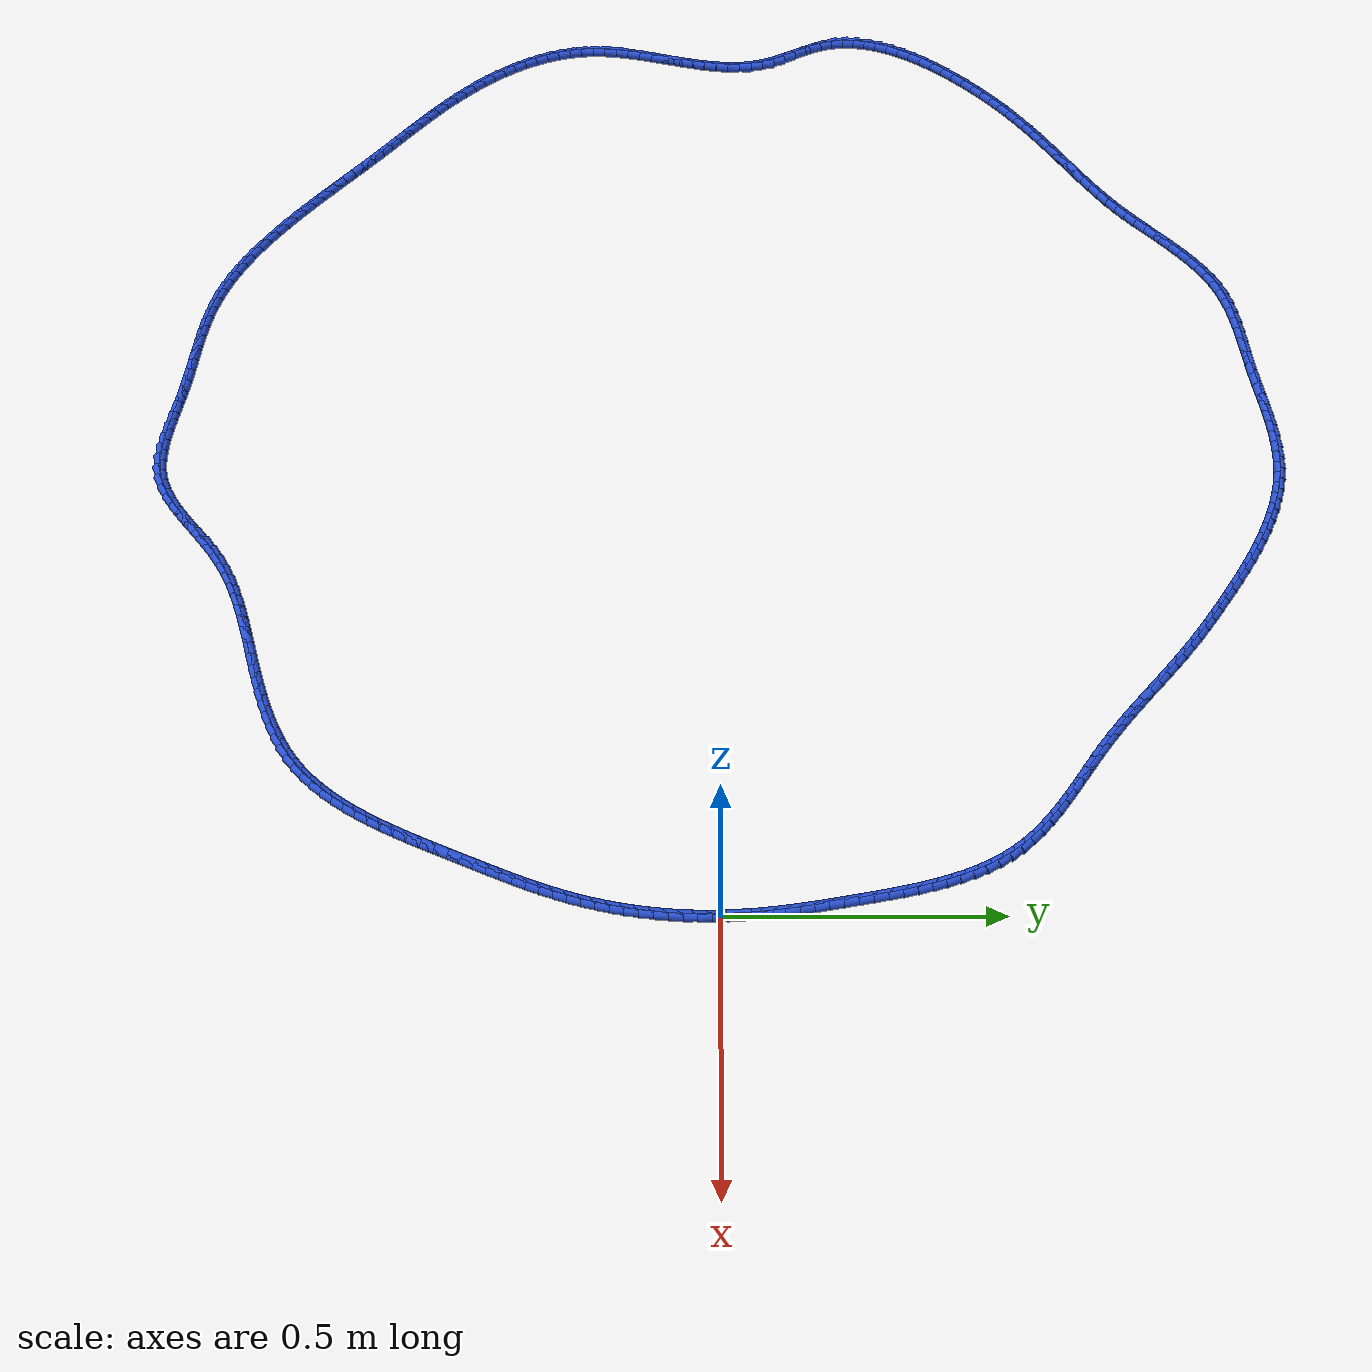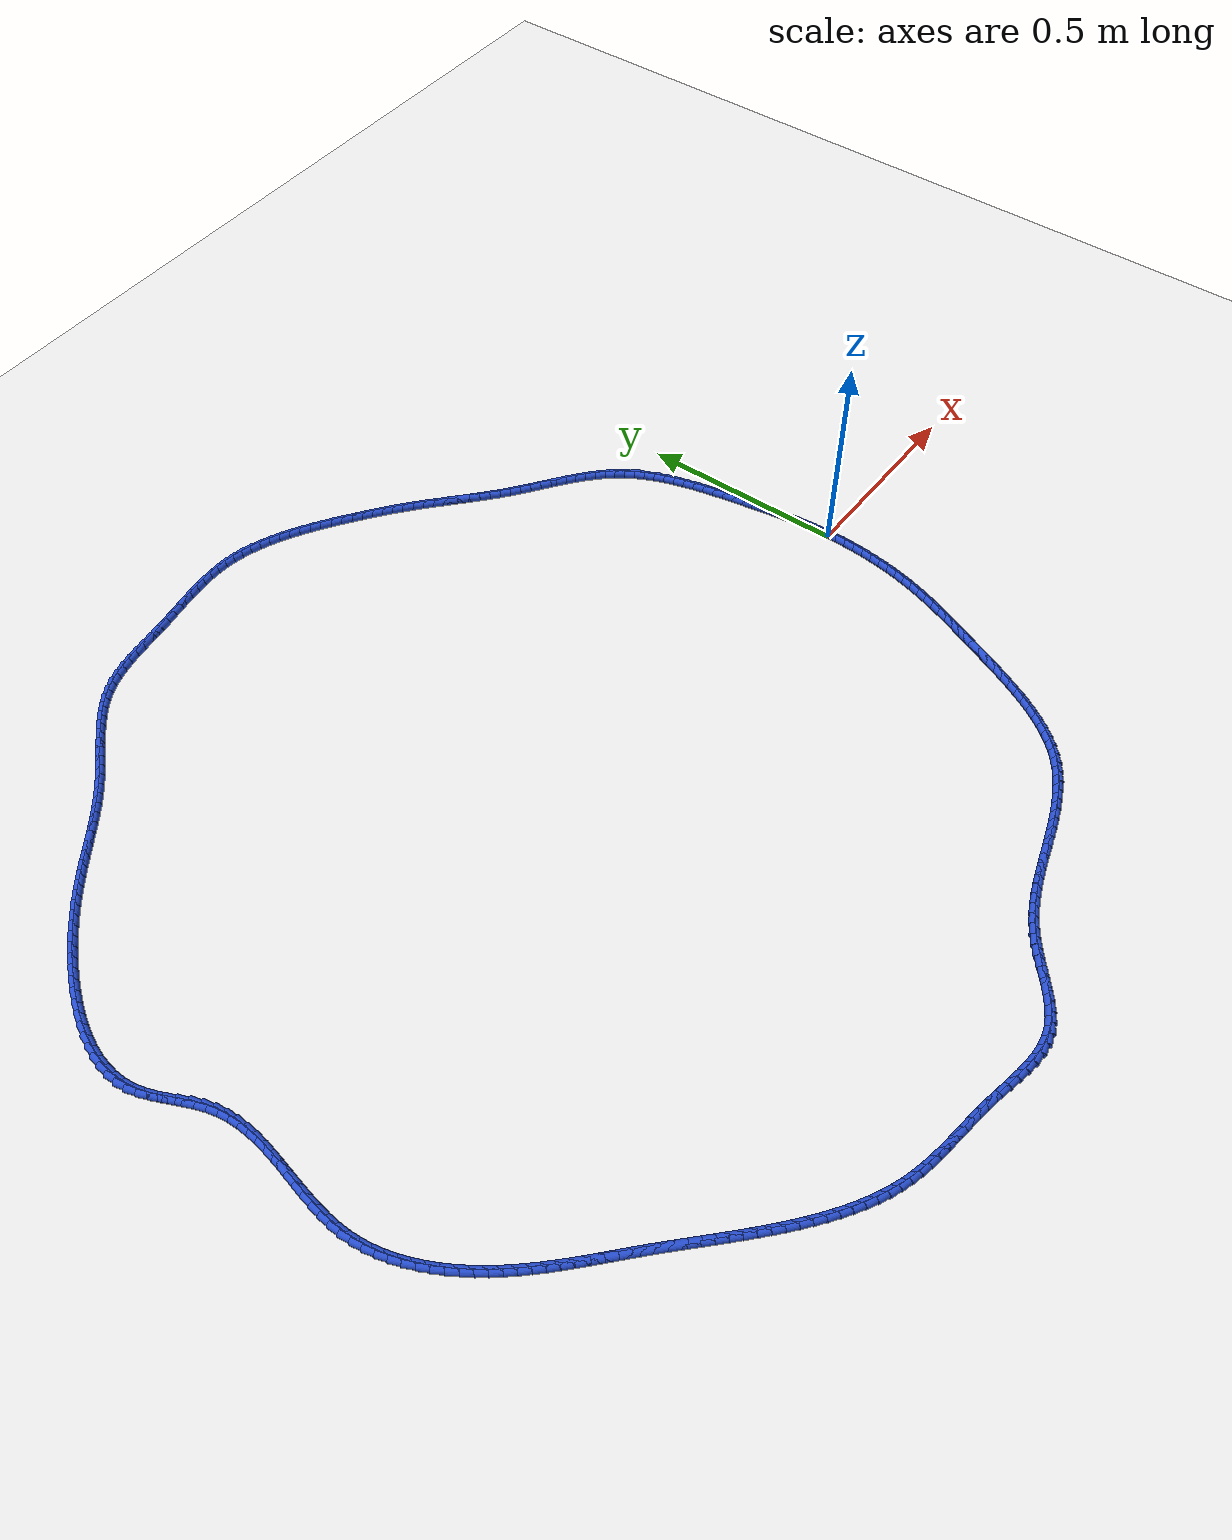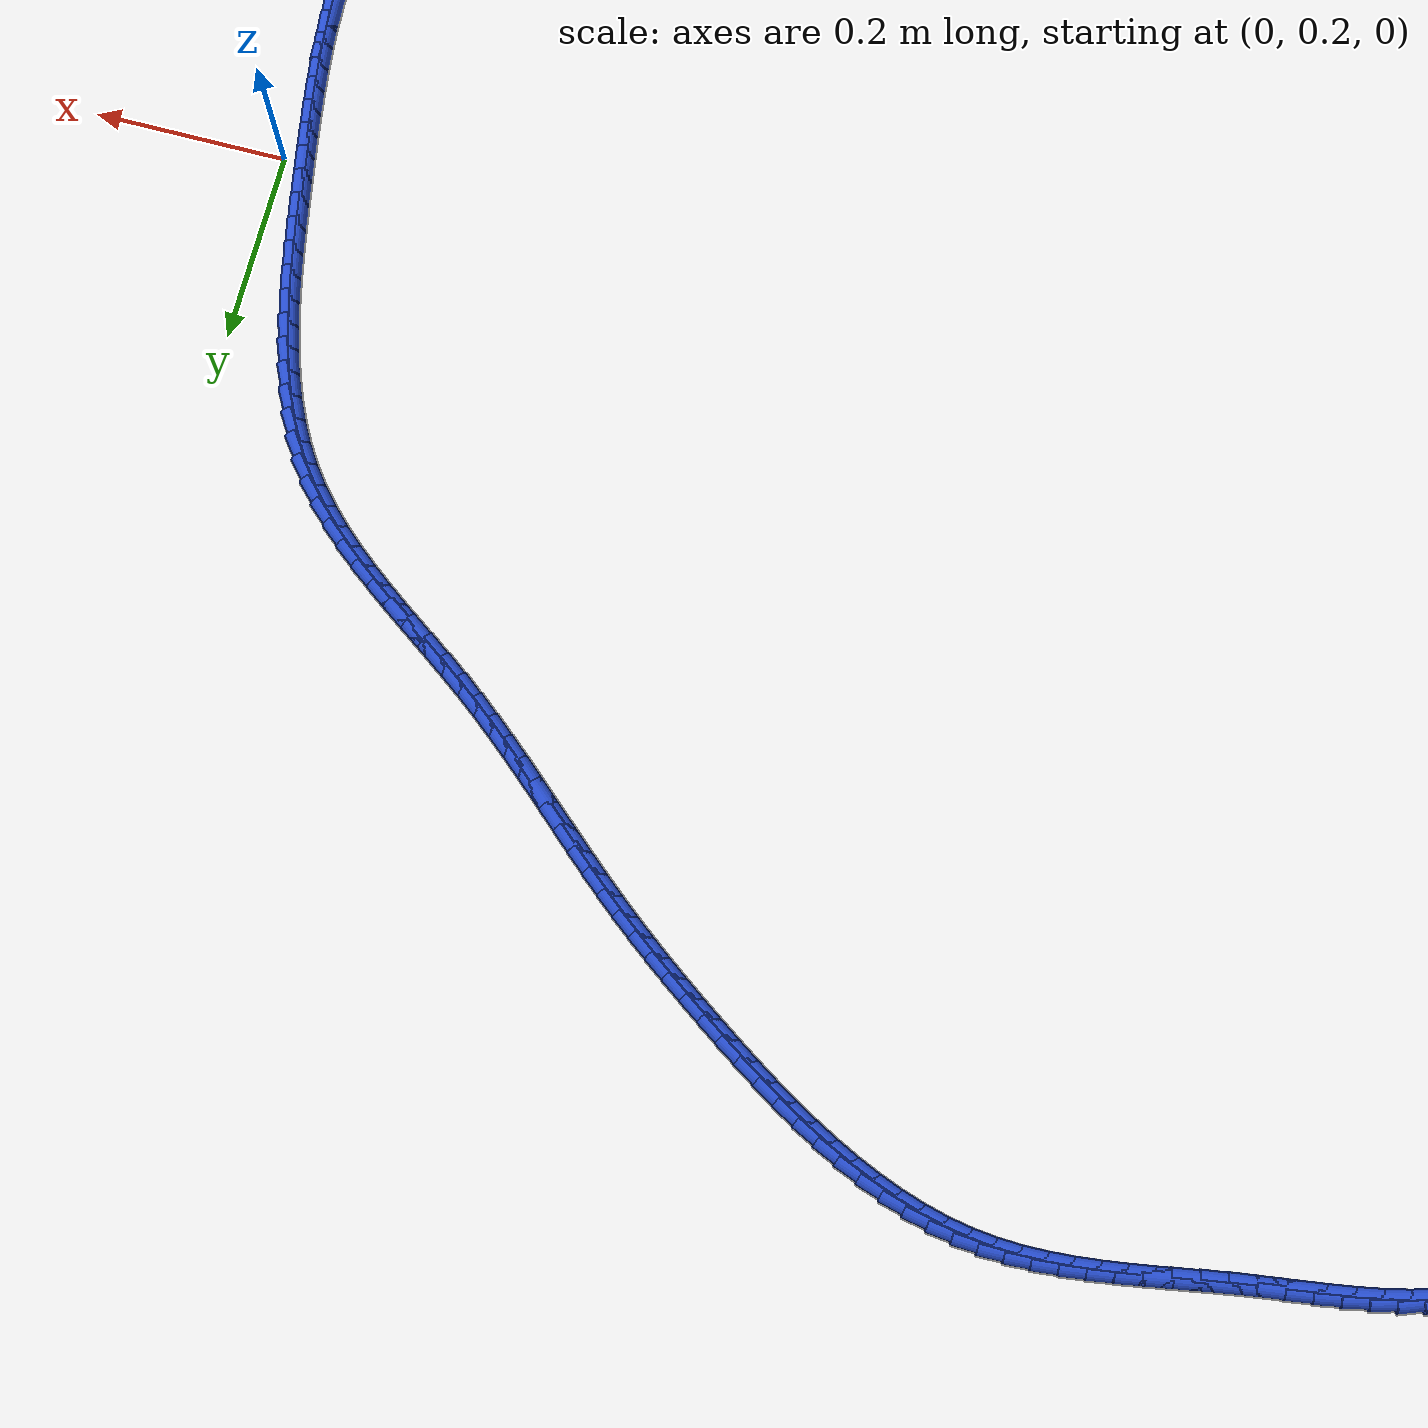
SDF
<sdf version="1.6">
 <world name="default">
  <light name="sun" type="directional">
   <pose>0 0 10 0 -0 0</pose>
   <diffuse>0.8 0.8 0.8 1</diffuse>
   <specular>0.2 0.2 0.2 1</specular>
   <attenuation>
    <range>1000</range>
    <constant>0.9</constant>
    <linear>0.01</linear>
    <quadratic>0.001</quadratic>
   </attenuation>
   <direction>-0.5 0.1 -0.9</direction>
  </light>
  <model name="ground_plane">
   <static>1</static>
   <link name="link">
    <collision name="collision">
     <geometry><plane><normal>0 0 1</normal><size>100 100</size></plane></geometry>
     <surface><friction><ode><mu>100</mu><mu2>50</mu2></ode></friction></surface>
    </collision>
    <visual name="visual">
     <cast_shadows>0</cast_shadows>
     <geometry><plane><normal>0 0 1</normal><size>100 100</size></plane></geometry>
     <material>
      <script><uri>file://media/materials/scripts/gazebo.material</uri><name>Gazebo/WhiteGlow</name></script>
     </material>
    </visual>
   </link>
  </model>
  <gravity>0 0 -9.8</gravity>
  <magnetic_field>6e-06 2.3e-05 -4.2e-05</magnetic_field>
  <atmosphere type="adiabatic"/>
  <physics name="default_physics" default="0" type="ode">
   <max_step_size>0.001</max_step_size>
   <real_time_factor>1</real_time_factor>
   <real_time_update_rate>1000</real_time_update_rate>
  </physics>
  <scene><ambient>0.4 0.4 0.4 1</ambient><background>0.7 0.7 0.7 1</background><shadows>1</shadows></scene>
  <spherical_coordinates>
   <surface_model>EARTH_WGS84</surface_model>
   <latitude_deg>0</latitude_deg>
   <longitude_deg>0</longitude_deg>
   <elevation>0</elevation>
   <heading_deg>0</heading_deg>
  </spherical_coordinates>
  <model name="line">
   <link name="link_0">
    <pose>-3.469446951953614e-18 -4.163336342344337e-17 0.01 0 1.57 -1.5361704127176894</pose>
    <collision name="collision">
     <geometry><cylinder><radius>0.01</radius><length>0.08</length></cylinder></geometry>
    </collision>
    <visual name="visual">
     <material>
      <script><name>Gazebo/Blue</name><uri>file://media/materials/scripts/gazebo.material</uri></script>
     </material>
     <geometry><cylinder><radius>0.01</radius><length>0.08</length></cylinder></geometry>
    </visual>
   </link>
   <link name="link_1">
    <pose>-0.000874193337033417 0.02523670377755948 0.01 0 1.57 -1.5087189368360825</pose>
    <collision name="collision">
     <geometry><cylinder><radius>0.01</radius><length>0.08</length></cylinder></geometry>
    </collision>
    <visual name="visual">
     <material>
      <script><name>Gazebo/Blue</name><uri>file://media/materials/scripts/gazebo.material</uri></script>
     </material>
     <geometry><cylinder><radius>0.01</radius><length>0.08</length></cylinder></geometry>
    </visual>
   </link>
   <link name="link_2">
    <pose>-0.0024369470741145123 0.05037864050720676 0.01 0 1.57 -1.4840330031197346</pose>
    <collision name="collision">
     <geometry><cylinder><radius>0.01</radius><length>0.08</length></cylinder></geometry>
    </collision>
    <visual name="visual">
     <material>
      <script><name>Gazebo/Blue</name><uri>file://media/materials/scripts/gazebo.material</uri></script>
     </material>
     <geometry><cylinder><radius>0.01</radius><length>0.08</length></cylinder></geometry>
    </visual>
   </link>
   <link name="link_3">
    <pose>-0.0046185864620653435 0.07546023232954456 0.01 0 1.57 -1.4622335359305623</pose>
    <collision name="collision">
     <geometry><cylinder><radius>0.01</radius><length>0.08</length></cylinder></geometry>
    </collision>
    <visual name="visual">
     <material>
      <script><name>Gazebo/Blue</name><uri>file://media/materials/scripts/gazebo.material</uri></script>
     </material>
     <geometry><cylinder><radius>0.01</radius><length>0.08</length></cylinder></geometry>
    </visual>
   </link>
   <link name="link_4">
    <pose>-0.007349436751707944 0.10051590138517547 0.01 0 1.57 -1.443403290524753</pose>
    <collision name="collision">
     <geometry><cylinder><radius>0.01</radius><length>0.08</length></cylinder></geometry>
    </collision>
    <visual name="visual">
     <material>
      <script><name>Gazebo/Blue</name><uri>file://media/materials/scripts/gazebo.material</uri></script>
     </material>
     <geometry><cylinder><radius>0.01</radius><length>0.08</length></cylinder></geometry>
    </visual>
   </link>
   <link name="link_5">
    <pose>-0.010559823193864367 0.12558006981470227 0.01 0 1.57 -1.4275911102858279</pose>
    <collision name="collision">
     <geometry><cylinder><radius>0.01</radius><length>0.08</length></cylinder></geometry>
    </collision>
    <visual name="visual">
     <material>
      <script><name>Gazebo/Blue</name><uri>file://media/materials/scripts/gazebo.material</uri></script>
     </material>
     <geometry><cylinder><radius>0.01</radius><length>0.08</length></cylinder></geometry>
    </visual>
   </link>
   <link name="link_6">
    <pose>-0.01418007103935665 0.15068715975872754 0.01 0 1.57 -1.4148165017263807</pose>
    <collision name="collision">
     <geometry><cylinder><radius>0.01</radius><length>0.08</length></cylinder></geometry>
    </collision>
    <visual name="visual">
     <material>
      <script><name>Gazebo/Blue</name><uri>file://media/materials/scripts/gazebo.material</uri></script>
     </material>
     <geometry><cylinder><radius>0.01</radius><length>0.08</length></cylinder></geometry>
    </visual>
   </link>
   <link name="link_7">
    <pose>-0.018140505539006858 0.17587159335785418 0.01 0 1.57 -1.4050740958365386</pose>
    <collision name="collision">
     <geometry><cylinder><radius>0.01</radius><length>0.08</length></cylinder></geometry>
    </collision>
    <visual name="visual">
     <material>
      <script><name>Gazebo/Blue</name><uri>file://media/materials/scripts/gazebo.material</uri></script>
     </material>
     <geometry><cylinder><radius>0.01</radius><length>0.08</length></cylinder></geometry>
    </visual>
   </link>
   <link name="link_8">
    <pose>-0.02237145194363701 0.2011677927526846 0.01 0 1.57 -1.3983376867380366</pose>
    <collision name="collision">
     <geometry><cylinder><radius>0.01</radius><length>0.08</length></cylinder></geometry>
    </collision>
    <visual name="visual">
     <material>
      <script><name>Gazebo/Blue</name><uri>file://media/materials/scripts/gazebo.material</uri></script>
     </material>
     <geometry><cylinder><radius>0.01</radius><length>0.08</length></cylinder></geometry>
    </visual>
   </link>
   <link name="link_9">
    <pose>-0.02680323550406917 0.2266101800838217 0.01 0 1.57 -1.3943841022933288</pose>
    <collision name="collision">
     <geometry><cylinder><radius>0.01</radius><length>0.08</length></cylinder></geometry>
    </collision>
    <visual name="visual">
     <material>
      <script><name>Gazebo/Blue</name><uri>file://media/materials/scripts/gazebo.material</uri></script>
     </material>
     <geometry><cylinder><radius>0.01</radius><length>0.08</length></cylinder></geometry>
    </visual>
   </link>
   <link name="link_10">
    <pose>-0.031370356107196 0.2522299681871698 0.01 0 1.57 -1.3891127773908747</pose>
    <collision name="collision">
     <geometry><cylinder><radius>0.01</radius><length>0.08</length></cylinder></geometry>
    </collision>
    <visual name="visual">
     <material>
      <script><name>Gazebo/Blue</name><uri>file://media/materials/scripts/gazebo.material</uri></script>
     </material>
     <geometry><cylinder><radius>0.01</radius><length>0.08</length></cylinder></geometry>
    </visual>
   </link>
   <link name="link_11">
    <pose>-0.03610191483901392 0.2779856440208299 0.01 0 1.57 -1.3785036608698533</pose>
    <collision name="collision">
     <geometry><cylinder><radius>0.01</radius><length>0.08</length></cylinder></geometry>
    </collision>
    <visual name="visual">
     <material>
      <script><name>Gazebo/Blue</name><uri>file://media/materials/scripts/gazebo.material</uri></script>
     </material>
     <geometry><cylinder><radius>0.01</radius><length>0.08</length></cylinder></geometry>
    </visual>
   </link>
   <link name="link_12">
    <pose>-0.041120834252594156 0.3037635680940372 0.01 0 1.57 -1.3623242053024893</pose>
    <collision name="collision">
     <geometry><cylinder><radius>0.01</radius><length>0.08</length></cylinder></geometry>
    </collision>
    <visual name="visual">
     <material>
      <script><name>Gazebo/Blue</name><uri>file://media/materials/scripts/gazebo.material</uri></script>
     </material>
     <geometry><cylinder><radius>0.01</radius><length>0.08</length></cylinder></geometry>
    </visual>
   </link>
   <link name="link_13">
    <pose>-0.046554055587323985 0.32944701149969036 0.01 0 1.57 -1.340412642717985</pose>
    <collision name="collision">
     <geometry><cylinder><radius>0.01</radius><length>0.08</length></cylinder></geometry>
    </collision>
    <visual name="visual">
     <material>
      <script><name>Gazebo/Blue</name><uri>file://media/materials/scripts/gazebo.material</uri></script>
     </material>
     <geometry><cylinder><radius>0.01</radius><length>0.08</length></cylinder></geometry>
    </visual>
   </link>
   <link name="link_14">
    <pose>-0.05252852008259073 0.3549192453306882 0.01 0 1.57 -1.312515869545272</pose>
    <collision name="collision">
     <geometry><cylinder><radius>0.01</radius><length>0.08</length></cylinder></geometry>
    </collision>
    <visual name="visual">
     <material>
      <script><name>Gazebo/Blue</name><uri>file://media/materials/scripts/gazebo.material</uri></script>
     </material>
     <geometry><cylinder><radius>0.01</radius><length>0.08</length></cylinder></geometry>
    </visual>
   </link>
   <link name="link_15">
    <pose>-0.05917116897778162 0.380063540679929 0.01 0 1.57 -1.2783040647329198</pose>
    <collision name="collision">
     <geometry><cylinder><radius>0.01</radius><length>0.08</length></cylinder></geometry>
    </collision>
    <visual name="visual">
     <material>
      <script><name>Gazebo/Blue</name><uri>file://media/materials/scripts/gazebo.material</uri></script>
     </material>
     <geometry><cylinder><radius>0.01</radius><length>0.08</length></cylinder></geometry>
    </visual>
   </link>
   <link name="link_16">
    <pose>-0.066608943512284 0.40476316864031187 0.01 0 1.57 -1.2373929668075934</pose>
    <collision name="collision">
     <geometry><cylinder><radius>0.01</radius><length>0.08</length></cylinder></geometry>
    </collision>
    <visual name="visual">
     <material>
      <script><name>Gazebo/Blue</name><uri>file://media/materials/scripts/gazebo.material</uri></script>
     </material>
     <geometry><cylinder><radius>0.01</radius><length>0.08</length></cylinder></geometry>
    </visual>
   </link>
   <link name="link_17">
    <pose>-0.07496878492548514 0.4289014003047354 0.01 0 1.57 -1.1893787220083807</pose>
    <collision name="collision">
     <geometry><cylinder><radius>0.01</radius><length>0.08</length></cylinder></geometry>
    </collision>
    <visual name="visual">
     <material>
      <script><name>Gazebo/Blue</name><uri>file://media/materials/scripts/gazebo.material</uri></script>
     </material>
     <geometry><cylinder><radius>0.01</radius><length>0.08</length></cylinder></geometry>
    </visual>
   </link>
   <link name="link_18">
    <pose>-0.08437763445677234 0.45236150676609815 0.01 0 1.57 -1.1338909140084628</pose>
    <collision name="collision">
     <geometry><cylinder><radius>0.01</radius><length>0.08</length></cylinder></geometry>
    </collision>
    <visual name="visual">
     <material>
      <script><name>Gazebo/Blue</name><uri>file://media/materials/scripts/gazebo.material</uri></script>
     </material>
     <geometry><cylinder><radius>0.01</radius><length>0.08</length></cylinder></geometry>
    </visual>
   </link>
   <link name="link_19">
    <pose>-0.09496243334553289 0.47502675911729897 0.01 0 1.57 -1.0706686797961786</pose>
    <collision name="collision">
     <geometry><cylinder><radius>0.01</radius><length>0.08</length></cylinder></geometry>
    </collision>
    <visual name="visual">
     <material>
      <script><name>Gazebo/Blue</name><uri>file://media/materials/scripts/gazebo.material</uri></script>
     </material>
     <geometry><cylinder><radius>0.01</radius><length>0.08</length></cylinder></geometry>
    </visual>
   </link>
   <link name="link_20">
    <pose>-0.10685012283115405 0.4967804284512364 0.01 0 1.57 -0.999661080159758</pose>
    <collision name="collision">
     <geometry><cylinder><radius>0.01</radius><length>0.08</length></cylinder></geometry>
    </collision>
    <visual name="visual">
     <material>
      <script><name>Gazebo/Blue</name><uri>file://media/materials/scripts/gazebo.material</uri></script>
     </material>
     <geometry><cylinder><radius>0.01</radius><length>0.08</length></cylinder></geometry>
    </visual>
   </link>
   <link name="link_21">
    <pose>-0.12016764415302318 0.5175057858608093 0.01 0 1.57 -0.921825333954852</pose>
    <collision name="collision">
     <geometry><cylinder><radius>0.01</radius><length>0.08</length></cylinder></geometry>
    </collision>
    <visual name="visual">
     <material>
      <script><name>Gazebo/Blue</name><uri>file://media/materials/scripts/gazebo.material</uri></script>
     </material>
     <geometry><cylinder><radius>0.01</radius><length>0.08</length></cylinder></geometry>
    </visual>
   </link>
   <link name="link_22">
    <pose>-0.13502901605710235 0.537096775593167 0.01 0 1.57 -0.8472271110047734</pose>
    <collision name="collision">
     <geometry><cylinder><radius>0.01</radius><length>0.08</length></cylinder></geometry>
    </collision>
    <visual name="visual">
     <material>
      <script><name>Gazebo/Blue</name><uri>file://media/materials/scripts/gazebo.material</uri></script>
     </material>
     <geometry><cylinder><radius>0.01</radius><length>0.08</length></cylinder></geometry>
    </visual>
   </link>
   <link name="link_23">
    <pose>-0.15137000946560114 0.55559456321376 0.01 0 1.57 -0.7833091684189385</pose>
    <collision name="collision">
     <geometry><cylinder><radius>0.01</radius><length>0.08</length></cylinder></geometry>
    </collision>
    <visual name="visual">
     <material>
      <script><name>Gazebo/Blue</name><uri>file://media/materials/scripts/gazebo.material</uri></script>
     </material>
     <geometry><cylinder><radius>0.01</radius><length>0.08</length></cylinder></geometry>
    </visual>
   </link>
   <link name="link_24">
    <pose>-0.1689965195687003 0.5731475833479461 0.01 0 1.57 -0.7303190272904614</pose>
    <collision name="collision">
     <geometry><cylinder><radius>0.01</radius><length>0.08</length></cylinder></geometry>
    </collision>
    <visual name="visual">
     <material>
      <script><name>Gazebo/Blue</name><uri>file://media/materials/scripts/gazebo.material</uri></script>
     </material>
     <geometry><cylinder><radius>0.01</radius><length>0.08</length></cylinder></geometry>
    </visual>
   </link>
   <link name="link_25">
    <pose>-0.18771149848549545 0.5899067014098354 0.01 0 1.57 -0.6880008195240946</pose>
    <collision name="collision">
     <geometry><cylinder><radius>0.01</radius><length>0.08</length></cylinder></geometry>
    </collision>
    <visual name="visual">
     <material>
      <script><name>Gazebo/Blue</name><uri>file://media/materials/scripts/gazebo.material</uri></script>
     </material>
     <geometry><cylinder><radius>0.01</radius><length>0.08</length></cylinder></geometry>
    </visual>
   </link>
   <link name="link_26">
    <pose>-0.20731789833508213 0.6060227828135373 0.01 0 1.57 -0.6559410225692032</pose>
    <collision name="collision">
     <geometry><cylinder><radius>0.01</radius><length>0.08</length></cylinder></geometry>
    </collision>
    <visual name="visual">
     <material>
      <script><name>Gazebo/Blue</name><uri>file://media/materials/scripts/gazebo.material</uri></script>
     </material>
     <geometry><cylinder><radius>0.01</radius><length>0.08</length></cylinder></geometry>
    </visual>
   </link>
   <link name="link_27">
    <pose>-0.22761867123655616 0.6216466929731622 0.01 0 1.57 -0.6337069792559067</pose>
    <collision name="collision">
     <geometry><cylinder><radius>0.01</radius><length>0.08</length></cylinder></geometry>
    </collision>
    <visual name="visual">
     <material>
      <script><name>Gazebo/Blue</name><uri>file://media/materials/scripts/gazebo.material</uri></script>
     </material>
     <geometry><cylinder><radius>0.01</radius><length>0.08</length></cylinder></geometry>
    </visual>
   </link>
   <link name="link_28">
    <pose>-0.24841676930901294 0.6369292973028194 0.01 0 1.57 -0.6209363376053827</pose>
    <collision name="collision">
     <geometry><cylinder><radius>0.01</radius><length>0.08</length></cylinder></geometry>
    </collision>
    <visual name="visual">
     <material>
      <script><name>Gazebo/Blue</name><uri>file://media/materials/scripts/gazebo.material</uri></script>
     </material>
     <geometry><cylinder><radius>0.01</radius><length>0.08</length></cylinder></geometry>
    </visual>
   </link>
   <link name="link_29">
    <pose>-0.26951514467154813 0.6520214612166191 0.01 0 1.57 -0.6173886294715584</pose>
    <collision name="collision">
     <geometry><cylinder><radius>0.01</radius><length>0.08</length></cylinder></geometry>
    </collision>
    <visual name="visual">
     <material>
      <script><name>Gazebo/Blue</name><uri>file://media/materials/scripts/gazebo.material</uri></script>
     </material>
     <geometry><cylinder><radius>0.01</radius><length>0.08</length></cylinder></geometry>
    </visual>
   </link>
   <link name="link_30">
    <pose>-0.2907167494432574 0.6670740501286709 0.01 0 1.57 -0.6229699389005323</pose>
    <collision name="collision">
     <geometry><cylinder><radius>0.01</radius><length>0.08</length></cylinder></geometry>
    </collision>
    <visual name="visual">
     <material>
      <script><name>Gazebo/Blue</name><uri>file://media/materials/scripts/gazebo.material</uri></script>
     </material>
     <geometry><cylinder><radius>0.01</radius><length>0.08</length></cylinder></geometry>
    </visual>
   </link>
   <link name="link_31">
    <pose>-0.3118245357432365 0.6822379294530851 0.01 0 1.57 -0.6377378107391887</pose>
    <collision name="collision">
     <geometry><cylinder><radius>0.01</radius><length>0.08</length></cylinder></geometry>
    </collision>
    <visual name="visual">
     <material>
      <script><name>Gazebo/Blue</name><uri>file://media/materials/scripts/gazebo.material</uri></script>
     </material>
     <geometry><cylinder><radius>0.01</radius><length>0.08</length></cylinder></geometry>
    </visual>
   </link>
   <link name="link_32">
    <pose>-0.3326414556905807 0.6976639646039708 0.01 0 1.57 -0.6606003936755541</pose>
    <collision name="collision">
     <geometry><cylinder><radius>0.01</radius><length>0.08</length></cylinder></geometry>
    </collision>
    <visual name="visual">
     <material>
      <script><name>Gazebo/Blue</name><uri>file://media/materials/scripts/gazebo.material</uri></script>
     </material>
     <geometry><cylinder><radius>0.01</radius><length>0.08</length></cylinder></geometry>
    </visual>
   </link>
   <link name="link_33">
    <pose>-0.3529966173404403 0.713481297053206 0.01 0 1.57 -0.6829501100329025</pose>
    <collision name="collision">
     <geometry><cylinder><radius>0.01</radius><length>0.08</length></cylinder></geometry>
    </collision>
    <visual name="visual">
     <material>
      <script><name>Gazebo/Blue</name><uri>file://media/materials/scripts/gazebo.material</uri></script>
     </material>
     <geometry><cylinder><radius>0.01</radius><length>0.08</length></cylinder></geometry>
    </visual>
   </link>
   <link name="link_34">
    <pose>-0.3728970221656594 0.729671318013548 0.01 0 1.57 -0.7010608413306577</pose>
    <collision name="collision">
     <geometry><cylinder><radius>0.01</radius><length>0.08</length></cylinder></geometry>
    </collision>
    <visual name="visual">
     <material>
      <script><name>Gazebo/Blue</name><uri>file://media/materials/scripts/gazebo.material</uri></script>
     </material>
     <geometry><cylinder><radius>0.01</radius><length>0.08</length></cylinder></geometry>
    </visual>
   </link>
   <link name="link_35">
    <pose>-0.39242374764037274 0.7461538945080071 0.01 0 1.57 -0.7148327995534279</pose>
    <collision name="collision">
     <geometry><cylinder><radius>0.01</radius><length>0.08</length></cylinder></geometry>
    </collision>
    <visual name="visual">
     <material>
      <script><name>Gazebo/Blue</name><uri>file://media/materials/scripts/gazebo.material</uri></script>
     </material>
     <geometry><cylinder><radius>0.01</radius><length>0.08</length></cylinder></geometry>
    </visual>
   </link>
   <link name="link_36">
    <pose>-0.4116581152209342 0.7628486909189514 0.01 0 1.57 -0.7242013201195109</pose>
    <collision name="collision">
     <geometry><cylinder><radius>0.01</radius><length>0.08</length></cylinder></geometry>
    </collision>
    <visual name="visual">
     <material>
      <script><name>Gazebo/Blue</name><uri>file://media/materials/scripts/gazebo.material</uri></script>
     </material>
     <geometry><cylinder><radius>0.01</radius><length>0.08</length></cylinder></geometry>
    </visual>
   </link>
   <link name="link_37">
    <pose>-0.43068144636369815 0.7796753716287501 0.01 0 1.57 -0.7291176338764762</pose>
    <collision name="collision">
     <geometry><cylinder><radius>0.01</radius><length>0.08</length></cylinder></geometry>
    </collision>
    <visual name="visual">
     <material>
      <script><name>Gazebo/Blue</name><uri>file://media/materials/scripts/gazebo.material</uri></script>
     </material>
     <geometry><cylinder><radius>0.01</radius><length>0.08</length></cylinder></geometry>
    </visual>
   </link>
   <link name="link_38">
    <pose>-0.4495750625250188 0.796553601019773 0.01 0 1.57 -0.7295437570549339</pose>
    <collision name="collision">
     <geometry><cylinder><radius>0.01</radius><length>0.08</length></cylinder></geometry>
    </collision>
    <visual name="visual">
     <material>
      <script><name>Gazebo/Blue</name><uri>file://media/materials/scripts/gazebo.material</uri></script>
     </material>
     <geometry><cylinder><radius>0.01</radius><length>0.08</length></cylinder></geometry>
    </visual>
   </link>
   <link name="link_39">
    <pose>-0.4684202851612497 0.813403043474388 0.01 0 1.57 -0.7254497983542078</pose>
    <collision name="collision">
     <geometry><cylinder><radius>0.01</radius><length>0.08</length></cylinder></geometry>
    </collision>
    <visual name="visual">
     <material>
      <script><name>Gazebo/Blue</name><uri>file://media/materials/scripts/gazebo.material</uri></script>
     </material>
     <geometry><cylinder><radius>0.01</radius><length>0.08</length></cylinder></geometry>
    </visual>
   </link>
   <link name="link_40">
    <pose>-0.48729843572874526 0.8301433633749645 0.01 0 1.57 -0.7168138878353535</pose>
    <collision name="collision">
     <geometry><cylinder><radius>0.01</radius><length>0.08</length></cylinder></geometry>
    </collision>
    <visual name="visual">
     <material>
      <script><name>Gazebo/Blue</name><uri>file://media/materials/scripts/gazebo.material</uri></script>
     </material>
     <geometry><cylinder><radius>0.01</radius><length>0.08</length></cylinder></geometry>
    </visual>
   </link>
   <link name="link_41">
    <pose>-0.5062908356838595 0.8466942251038714 0.01 0 1.57 -0.7036248560805604</pose>
    <collision name="collision">
     <geometry><cylinder><radius>0.01</radius><length>0.08</length></cylinder></geometry>
    </collision>
    <visual name="visual">
     <material>
      <script><name>Gazebo/Blue</name><uri>file://media/materials/scripts/gazebo.material</uri></script>
     </material>
     <geometry><cylinder><radius>0.01</radius><length>0.08</length></cylinder></geometry>
    </visual>
   </link>
   <link name="link_42">
    <pose>-0.5254788064829464 0.8629752930434779 0.01 0 1.57 -0.6861760715650963</pose>
    <collision name="collision">
     <geometry><cylinder><radius>0.01</radius><length>0.08</length></cylinder></geometry>
    </collision>
    <visual name="visual">
     <material>
      <script><name>Gazebo/Blue</name><uri>file://media/materials/scripts/gazebo.material</uri></script>
     </material>
     <geometry><cylinder><radius>0.01</radius><length>0.08</length></cylinder></geometry>
    </visual>
   </link>
   <link name="link_43">
    <pose>-0.5449400351968171 0.8789126301467078 0.01 0 1.57 -0.667919222868921</pose>
    <collision name="collision">
     <geometry><cylinder><radius>0.01</radius><length>0.08</length></cylinder></geometry>
    </collision>
    <visual name="visual">
     <material>
      <script><name>Gazebo/Blue</name><uri>file://media/materials/scripts/gazebo.material</uri></script>
     </material>
     <geometry><cylinder><radius>0.01</radius><length>0.08</length></cylinder></geometry>
    </visual>
   </link>
   <link name="link_44">
    <pose>-0.5647092118277424 0.8945079984835582 0.01 0 1.57 -0.651163459229971</pose>
    <collision name="collision">
     <geometry><cylinder><radius>0.01</radius><length>0.08</length></cylinder></geometry>
    </collision>
    <visual name="visual">
     <material>
      <script><name>Gazebo/Blue</name><uri>file://media/materials/scripts/gazebo.material</uri></script>
     </material>
     <geometry><cylinder><radius>0.01</radius><length>0.08</length></cylinder></geometry>
    </visual>
   </link>
   <link name="link_45">
    <pose>-0.5847929272959351 0.909812630373385 0.01 0 1.57 -0.6360166915280844</pose>
    <collision name="collision">
     <geometry><cylinder><radius>0.01</radius><length>0.08</length></cylinder></geometry>
    </collision>
    <visual name="visual">
     <material>
      <script><name>Gazebo/Blue</name><uri>file://media/materials/scripts/gazebo.material</uri></script>
     </material>
     <geometry><cylinder><radius>0.01</radius><length>0.08</length></cylinder></geometry>
    </visual>
   </link>
   <link name="link_46">
    <pose>-0.605197287805426 0.9248786115096992 0.01 0 1.57 -0.6225288436877654</pose>
    <collision name="collision">
     <geometry><cylinder><radius>0.01</radius><length>0.08</length></cylinder></geometry>
    </collision>
    <visual name="visual">
     <material>
      <script><name>Gazebo/Blue</name><uri>file://media/materials/scripts/gazebo.material</uri></script>
     </material>
     <geometry><cylinder><radius>0.01</radius><length>0.08</length></cylinder></geometry>
    </visual>
   </link>
   <link name="link_47">
    <pose>-0.6259283995602454 0.9397580275860117 0.01 0 1.57 -0.6107310070769285</pose>
    <collision name="collision">
     <geometry><cylinder><radius>0.01</radius><length>0.08</length></cylinder></geometry>
    </collision>
    <visual name="visual">
     <material>
      <script><name>Gazebo/Blue</name><uri>file://media/materials/scripts/gazebo.material</uri></script>
     </material>
     <geometry><cylinder><radius>0.01</radius><length>0.08</length></cylinder></geometry>
    </visual>
   </link>
   <link name="link_48">
    <pose>-0.6469923687644236 0.9545029642958331 0.01 0 1.57 -0.6001465090100524</pose>
    <collision name="collision">
     <geometry><cylinder><radius>0.01</radius><length>0.08</length></cylinder></geometry>
    </collision>
    <visual name="visual">
     <material>
      <script><name>Gazebo/Blue</name><uri>file://media/materials/scripts/gazebo.material</uri></script>
     </material>
     <geometry><cylinder><radius>0.01</radius><length>0.08</length></cylinder></geometry>
    </visual>
   </link>
   <link name="link_49">
    <pose>-0.6683937288089691 0.9691490259500634 0.01 0 1.57 -0.5870535563652751</pose>
    <collision name="collision">
     <geometry><cylinder><radius>0.01</radius><length>0.08</length></cylinder></geometry>
    </collision>
    <visual name="visual">
     <material>
      <script><name>Gazebo/Blue</name><uri>file://media/materials/scripts/gazebo.material</uri></script>
     </material>
     <geometry><cylinder><radius>0.01</radius><length>0.08</length></cylinder></geometry>
    </visual>
   </link>
   <link name="link_50">
    <pose>-0.6901250851858581 0.9836068253539899 0.01 0 1.57 -0.5696935325997188</pose>
    <collision name="collision">
     <geometry><cylinder><radius>0.01</radius><length>0.08</length></cylinder></geometry>
    </collision>
    <visual name="visual">
     <material>
      <script><name>Gazebo/Blue</name><uri>file://media/materials/scripts/gazebo.material</uri></script>
     </material>
     <geometry><cylinder><radius>0.01</radius><length>0.08</length></cylinder></geometry>
    </visual>
   </link>
   <link name="link_51">
    <pose>-0.7121735760202119 0.9977296832103163 0.01 0 1.57 -0.5479281256998118</pose>
    <collision name="collision">
     <geometry><cylinder><radius>0.01</radius><length>0.08</length></cylinder></geometry>
    </collision>
    <visual name="visual">
     <material>
      <script><name>Gazebo/Blue</name><uri>file://media/materials/scripts/gazebo.material</uri></script>
     </material>
     <geometry><cylinder><radius>0.01</radius><length>0.08</length></cylinder></geometry>
    </visual>
   </link>
   <link name="link_52">
    <pose>-0.7345263109401052 1.0113706216034608 0.01 0 1.57 -0.5215584401308614</pose>
    <collision name="collision">
     <geometry><cylinder><radius>0.01</radius><length>0.08</length></cylinder></geometry>
    </collision>
    <visual name="visual">
     <material>
      <script><name>Gazebo/Blue</name><uri>file://media/materials/scripts/gazebo.material</uri></script>
     </material>
     <geometry><cylinder><radius>0.01</radius><length>0.08</length></cylinder></geometry>
    </visual>
   </link>
   <link name="link_53">
    <pose>-0.7571703995736125 1.0243826626178403 0.01 0 1.57 -0.49032422655534197</pose>
    <collision name="collision">
     <geometry><cylinder><radius>0.01</radius><length>0.08</length></cylinder></geometry>
    </collision>
    <visual name="visual">
     <material>
      <script><name>Gazebo/Blue</name><uri>file://media/materials/scripts/gazebo.material</uri></script>
     </material>
     <geometry><cylinder><radius>0.01</radius><length>0.08</length></cylinder></geometry>
    </visual>
   </link>
   <link name="link_54">
    <pose>-0.7800929515488084 1.0366188283378728 0.01 0 1.57 -0.4539147878214248</pose>
    <collision name="collision">
     <geometry><cylinder><radius>0.01</radius><length>0.08</length></cylinder></geometry>
    </collision>
    <visual name="visual">
     <material>
      <script><name>Gazebo/Blue</name><uri>file://media/materials/scripts/gazebo.material</uri></script>
     </material>
     <geometry><cylinder><radius>0.01</radius><length>0.08</length></cylinder></geometry>
    </visual>
   </link>
   <link name="link_55">
    <pose>-0.8032810764937679 1.0479321408479756 0.01 0 1.57 -0.41198526524598034</pose>
    <collision name="collision">
     <geometry><cylinder><radius>0.01</radius><length>0.08</length></cylinder></geometry>
    </collision>
    <visual name="visual">
     <material>
      <script><name>Gazebo/Blue</name><uri>file://media/materials/scripts/gazebo.material</uri></script>
     </material>
     <geometry><cylinder><radius>0.01</radius><length>0.08</length></cylinder></geometry>
    </visual>
   </link>
   <link name="link_56">
    <pose>-0.826721884036565 1.058175622232566 0.01 0 1.57 -0.36418144966591903</pose>
    <collision name="collision">
     <geometry><cylinder><radius>0.01</radius><length>0.08</length></cylinder></geometry>
    </collision>
    <visual name="visual">
     <material>
      <script><name>Gazebo/Blue</name><uri>file://media/materials/scripts/gazebo.material</uri></script>
     </material>
     <geometry><cylinder><radius>0.01</radius><length>0.08</length></cylinder></geometry>
    </visual>
   </link>
   <link name="link_57">
    <pose>-0.8504024838052747 1.0672022945760624 0.01 0 1.57 -0.3101765805159727</pose>
    <collision name="collision">
     <geometry><cylinder><radius>0.01</radius><length>0.08</length></cylinder></geometry>
    </collision>
    <visual name="visual">
     <material>
      <script><name>Gazebo/Blue</name><uri>file://media/materials/scripts/gazebo.material</uri></script>
     </material>
     <geometry><cylinder><radius>0.01</radius><length>0.08</length></cylinder></geometry>
    </visual>
   </link>
   <link name="link_58">
    <pose>-0.8743099854279718 1.0748651799628821 0.01 0 1.57 -0.24972314839626608</pose>
    <collision name="collision">
     <geometry><cylinder><radius>0.01</radius><length>0.08</length></cylinder></geometry>
    </collision>
    <visual name="visual">
     <material>
      <script><name>Gazebo/Blue</name><uri>file://media/materials/scripts/gazebo.material</uri></script>
     </material>
     <geometry><cylinder><radius>0.01</radius><length>0.08</length></cylinder></geometry>
    </visual>
   </link>
   <link name="link_59">
    <pose>-0.8984314985327306 1.081017300477442 0.01 0 1.57 -0.18272068318258286</pose>
    <collision name="collision">
     <geometry><cylinder><radius>0.01</radius><length>0.08</length></cylinder></geometry>
    </collision>
    <visual name="visual">
     <material>
      <script><name>Gazebo/Blue</name><uri>file://media/materials/scripts/gazebo.material</uri></script>
     </material>
     <geometry><cylinder><radius>0.01</radius><length>0.08</length></cylinder></geometry>
    </visual>
   </link>
   <link name="link_60">
    <pose>-0.9227541327476254 1.08551167820416 0.01 0 1.57 -0.10997051564813641</pose>
    <collision name="collision">
     <geometry><cylinder><radius>0.01</radius><length>0.08</length></cylinder></geometry>
    </collision>
    <visual name="visual">
     <material>
      <script><name>Gazebo/Blue</name><uri>file://media/materials/scripts/gazebo.material</uri></script>
     </material>
     <geometry><cylinder><radius>0.01</radius><length>0.08</length></cylinder></geometry>
    </visual>
   </link>
   <link name="link_61">
    <pose>-0.9472652169422685 1.0882180936027712 0.01 0 1.57 -0.0405916437221647</pose>
    <collision name="collision">
     <geometry><cylinder><radius>0.01</radius><length>0.08</length></cylinder></geometry>
    </collision>
    <visual name="visual">
     <material>
      <script><name>Gazebo/Blue</name><uri>file://media/materials/scripts/gazebo.material</uri></script>
     </material>
     <geometry><cylinder><radius>0.01</radius><length>0.08</length></cylinder></geometry>
    </visual>
   </link>
   <link name="link_62">
    <pose>-0.9719548863345251 1.089220838661706 0.01 0 1.57 0.018833948515527273</pose>
    <collision name="collision">
     <geometry><cylinder><radius>0.01</radius><length>0.08</length></cylinder></geometry>
    </collision>
    <visual name="visual">
     <material>
      <script><name>Gazebo/Blue</name><uri>file://media/materials/scripts/gazebo.material</uri></script>
     </material>
     <geometry><cylinder><radius>0.01</radius><length>0.08</length></cylinder></geometry>
    </visual>
   </link>
   <link name="link_63">
    <pose>-0.9968152170592917 1.0887525651031538 0.01 0 1.57 0.06797931857357559</pose>
    <collision name="collision">
     <geometry><cylinder><radius>0.01</radius><length>0.08</length></cylinder></geometry>
    </collision>
    <visual name="visual">
     <material>
      <script><name>Gazebo/Blue</name><uri>file://media/materials/scripts/gazebo.material</uri></script>
     </material>
     <geometry><cylinder><radius>0.01</radius><length>0.08</length></cylinder></geometry>
    </visual>
   </link>
   <link name="link_64">
    <pose>-1.021838323995918 1.0870488861961138 0.01 0 1.57 0.10696452530332518</pose>
    <collision name="collision">
     <geometry><cylinder><radius>0.01</radius><length>0.08</length></cylinder></geometry>
    </collision>
    <visual name="visual">
     <material>
      <script><name>Gazebo/Blue</name><uri>file://media/materials/scripts/gazebo.material</uri></script>
     </material>
     <geometry><cylinder><radius>0.01</radius><length>0.08</length></cylinder></geometry>
    </visual>
   </link>
   <link name="link_65">
    <pose>-1.0470163220237536 1.0843454152095848 0.01 0 1.57 0.13607970382046422</pose>
    <collision name="collision">
     <geometry><cylinder><radius>0.01</radius><length>0.08</length></cylinder></geometry>
    </collision>
    <visual name="visual">
     <material>
      <script><name>Gazebo/Blue</name><uri>file://media/materials/scripts/gazebo.material</uri></script>
     </material>
     <geometry><cylinder><radius>0.01</radius><length>0.08</length></cylinder></geometry>
    </visual>
   </link>
   <link name="link_66">
    <pose>-1.0723413260221488 1.0808777654125654 0.01 0 1.57 0.15566545825354128</pose>
    <collision name="collision">
     <geometry><cylinder><radius>0.01</radius><length>0.08</length></cylinder></geometry>
    </collision>
    <visual name="visual">
     <material>
      <script><name>Gazebo/Blue</name><uri>file://media/materials/scripts/gazebo.material</uri></script>
     </material>
     <geometry><cylinder><radius>0.01</radius><length>0.08</length></cylinder></geometry>
    </visual>
   </link>
   <link name="link_67">
    <pose>-1.0978054508704527 1.076881550074054 0.01 0 1.57 0.1660332832334869</pose>
    <collision name="collision">
     <geometry><cylinder><radius>0.01</radius><length>0.08</length></cylinder></geometry>
    </collision>
    <visual name="visual">
     <material>
      <script><name>Gazebo/Blue</name><uri>file://media/materials/scripts/gazebo.material</uri></script>
     </material>
     <geometry><cylinder><radius>0.01</radius><length>0.08</length></cylinder></geometry>
    </visual>
   </link>
   <link name="link_68">
    <pose>-1.1234008114480145 1.072592382463049 0.01 0 1.57 0.16741976443266116</pose>
    <collision name="collision">
     <geometry><cylinder><radius>0.01</radius><length>0.08</length></cylinder></geometry>
    </collision>
    <visual name="visual">
     <material>
      <script><name>Gazebo/Blue</name><uri>file://media/materials/scripts/gazebo.material</uri></script>
     </material>
     <geometry><cylinder><radius>0.01</radius><length>0.08</length></cylinder></geometry>
    </visual>
   </link>
   <link name="link_69">
    <pose>-1.1491195226341842 1.06824587584855 0.01 0 1.57 0.15996705940471143</pose>
    <collision name="collision">
     <geometry><cylinder><radius>0.01</radius><length>0.08</length></cylinder></geometry>
    </collision>
    <visual name="visual">
     <material>
      <script><name>Gazebo/Blue</name><uri>file://media/materials/scripts/gazebo.material</uri></script>
     </material>
     <geometry><cylinder><radius>0.01</radius><length>0.08</length></cylinder></geometry>
    </visual>
   </link>
   <link name="link_70">
    <pose>-1.1749536993083116 1.0640776434995542 0.01 0 1.57 0.14477655010999727</pose>
    <collision name="collision">
     <geometry><cylinder><radius>0.01</radius><length>0.08</length></cylinder></geometry>
    </collision>
    <visual name="visual">
     <material>
      <script><name>Gazebo/Blue</name><uri>file://media/materials/scripts/gazebo.material</uri></script>
     </material>
     <geometry><cylinder><radius>0.01</radius><length>0.08</length></cylinder></geometry>
    </visual>
   </link>
   <link name="link_71">
    <pose>-1.2008889509218494 1.0602963714527576 0.01 0 1.57 0.1342856530380723</pose>
    <collision name="collision">
     <geometry><cylinder><radius>0.01</radius><length>0.08</length></cylinder></geometry>
    </collision>
    <visual name="visual">
     <material>
      <script><name>Gazebo/Blue</name><uri>file://media/materials/scripts/gazebo.material</uri></script>
     </material>
     <geometry><cylinder><radius>0.01</radius><length>0.08</length></cylinder></geometry>
    </visual>
   </link>
   <link name="link_72">
    <pose>-1.226833703680876 1.056791269269033 0.01 0 1.57 0.13663447258557715</pose>
    <collision name="collision">
     <geometry><cylinder><radius>0.01</radius><length>0.08</length></cylinder></geometry>
    </collision>
    <visual name="visual">
     <material>
      <script><name>Gazebo/Blue</name><uri>file://media/materials/scripts/gazebo.material</uri></script>
     </material>
     <geometry><cylinder><radius>0.01</radius><length>0.08</length></cylinder></geometry>
    </visual>
   </link>
   <link name="link_73">
    <pose>-1.2526458383988395 1.0532423292908184 0.01 0 1.57 0.15217949498837913</pose>
    <collision name="collision">
     <geometry><cylinder><radius>0.01</radius><length>0.08</length></cylinder></geometry>
    </collision>
    <visual name="visual">
     <material>
      <script><name>Gazebo/Blue</name><uri>file://media/materials/scripts/gazebo.material</uri></script>
     </material>
     <geometry><cylinder><radius>0.01</radius><length>0.08</length></cylinder></geometry>
    </visual>
   </link>
   <link name="link_74">
    <pose>-1.2781823591318762 1.0493259147913858 0.01 0 1.57 0.18141897212784483</pose>
    <collision name="collision">
     <geometry><cylinder><radius>0.01</radius><length>0.08</length></cylinder></geometry>
    </collision>
    <visual name="visual">
     <material>
      <script><name>Gazebo/Blue</name><uri>file://media/materials/scripts/gazebo.material</uri></script>
     </material>
     <geometry><cylinder><radius>0.01</radius><length>0.08</length></cylinder></geometry>
    </visual>
   </link>
   <link name="link_75">
    <pose>-1.3033002699361227 1.0447183890440086 0.01 0 1.57 0.2250750815314255</pose>
    <collision name="collision">
     <geometry><cylinder><radius>0.01</radius><length>0.08</length></cylinder></geometry>
    </collision>
    <visual name="visual">
     <material>
      <script><name>Gazebo/Blue</name><uri>file://media/materials/scripts/gazebo.material</uri></script>
     </material>
     <geometry><cylinder><radius>0.01</radius><length>0.08</length></cylinder></geometry>
    </visual>
   </link>
   <link name="link_76">
    <pose>-1.327856574867715 1.0390961153219587 0.01 0 1.57 0.28394524503124924</pose>
    <collision name="collision">
     <geometry><cylinder><radius>0.01</radius><length>0.08</length></cylinder></geometry>
    </collision>
    <visual name="visual">
     <material>
      <script><name>Gazebo/Blue</name><uri>file://media/materials/scripts/gazebo.material</uri></script>
     </material>
     <geometry><cylinder><radius>0.01</radius><length>0.08</length></cylinder></geometry>
    </visual>
   </link>
   <link name="link_77">
    <pose>-1.3517082779827896 1.032135456898509 0.01 0 1.57 0.358623566309431</pose>
    <collision name="collision">
     <geometry><cylinder><radius>0.01</radius><length>0.08</length></cylinder></geometry>
    </collision>
    <visual name="visual">
     <material>
      <script><name>Gazebo/Blue</name><uri>file://media/materials/scripts/gazebo.material</uri></script>
     </material>
     <geometry><cylinder><radius>0.01</radius><length>0.08</length></cylinder></geometry>
    </visual>
   </link>
   <link name="link_78">
    <pose>-1.3747123833374835 1.0235127770469326 0.01 0 1.57 0.44777555967327</pose>
    <collision name="collision">
     <geometry><cylinder><radius>0.01</radius><length>0.08</length></cylinder></geometry>
    </collision>
    <visual name="visual">
     <material>
      <script><name>Gazebo/Blue</name><uri>file://media/materials/scripts/gazebo.material</uri></script>
     </material>
     <geometry><cylinder><radius>0.01</radius><length>0.08</length></cylinder></geometry>
    </visual>
   </link>
   <link name="link_79">
    <pose>-1.3967395407412524 1.012932813736701 0.01 0 1.57 0.5351571665505088</pose>
    <collision name="collision">
     <geometry><cylinder><radius>0.01</radius><length>0.08</length></cylinder></geometry>
    </collision>
    <visual name="visual">
     <material>
      <script><name>Gazebo/Blue</name><uri>file://media/materials/scripts/gazebo.material</uri></script>
     </material>
     <geometry><cylinder><radius>0.01</radius><length>0.08</length></cylinder></geometry>
    </visual>
   </link>
   <link name="link_80">
    <pose>-1.4178210324414733 1.000434320694365 0.01 0 1.57 0.6097517194103494</pose>
    <collision name="collision">
     <geometry><cylinder><radius>0.01</radius><length>0.08</length></cylinder></geometry>
    </collision>
    <visual name="visual">
     <material>
      <script><name>Gazebo/Blue</name><uri>file://media/materials/scripts/gazebo.material</uri></script>
     </material>
     <geometry><cylinder><radius>0.01</radius><length>0.08</length></cylinder></geometry>
    </visual>
   </link>
   <link name="link_81">
    <pose>-1.4380927324354231 0.9862735375601418 0.01 0 1.57 0.6711048671441473</pose>
    <collision name="collision">
     <geometry><cylinder><radius>0.01</radius><length>0.08</length></cylinder></geometry>
    </collision>
    <visual name="visual">
     <material>
      <script><name>Gazebo/Blue</name><uri>file://media/materials/scripts/gazebo.material</uri></script>
     </material>
     <geometry><cylinder><radius>0.01</radius><length>0.08</length></cylinder></geometry>
    </visual>
   </link>
   <link name="link_82">
    <pose>-1.457692301462862 0.9707104192894803 0.01 0 1.57 0.7195287915803439</pose>
    <collision name="collision">
     <geometry><cylinder><radius>0.01</radius><length>0.08</length></cylinder></geometry>
    </collision>
    <visual name="visual">
     <material>
      <script><name>Gazebo/Blue</name><uri>file://media/materials/scripts/gazebo.material</uri></script>
     </material>
     <geometry><cylinder><radius>0.01</radius><length>0.08</length></cylinder></geometry>
    </visual>
   </link>
   <link name="link_83">
    <pose>-1.476757400263548 0.9540049208378285 0.01 0 1.57 0.7556088954026524</pose>
    <collision name="collision">
     <geometry><cylinder><radius>0.01</radius><length>0.08</length></cylinder></geometry>
    </collision>
    <visual name="visual">
     <material>
      <script><name>Gazebo/Blue</name><uri>file://media/materials/scripts/gazebo.material</uri></script>
     </material>
     <geometry><cylinder><radius>0.01</radius><length>0.08</length></cylinder></geometry>
    </visual>
   </link>
   <link name="link_84">
    <pose>-1.4954256895772404 0.9364169971606363 0.01 0 1.57 0.7799708779220451</pose>
    <collision name="collision">
     <geometry><cylinder><radius>0.01</radius><length>0.08</length></cylinder></geometry>
    </collision>
    <visual name="visual">
     <material>
      <script><name>Gazebo/Blue</name><uri>file://media/materials/scripts/gazebo.material</uri></script>
     </material>
     <geometry><cylinder><radius>0.01</radius><length>0.08</length></cylinder></geometry>
    </visual>
   </link>
   <link name="link_85">
    <pose>-1.5138348301436997 0.9182066032133522 0.01 0 1.57 0.7931368139894777</pose>
    <collision name="collision">
     <geometry><cylinder><radius>0.01</radius><length>0.08</length></cylinder></geometry>
    </collision>
    <visual name="visual">
     <material>
      <script><name>Gazebo/Blue</name><uri>file://media/materials/scripts/gazebo.material</uri></script>
     </material>
     <geometry><cylinder><radius>0.01</radius><length>0.08</length></cylinder></geometry>
    </visual>
   </link>
   <link name="link_86">
    <pose>-1.5321224827026845 0.8996336939514247 0.01 0 1.57 0.7954478903864148</pose>
    <collision name="collision">
     <geometry><cylinder><radius>0.01</radius><length>0.08</length></cylinder></geometry>
    </collision>
    <visual name="visual">
     <material>
      <script><name>Gazebo/Blue</name><uri>file://media/materials/scripts/gazebo.material</uri></script>
     </material>
     <geometry><cylinder><radius>0.01</radius><length>0.08</length></cylinder></geometry>
    </visual>
   </link>
   <link name="link_87">
    <pose>-1.5504263079939526 0.8809582243303026 0.01 0 1.57 0.7870321054886239</pose>
    <collision name="collision">
     <geometry><cylinder><radius>0.01</radius><length>0.08</length></cylinder></geometry>
    </collision>
    <visual name="visual">
     <material>
      <script><name>Gazebo/Blue</name><uri>file://media/materials/scripts/gazebo.material</uri></script>
     </material>
     <geometry><cylinder><radius>0.01</radius><length>0.08</length></cylinder></geometry>
    </visual>
   </link>
   <link name="link_88">
    <pose>-1.5688839667572656 0.8624401493054352 0.01 0 1.57 0.767803516785422</pose>
    <collision name="collision">
     <geometry><cylinder><radius>0.01</radius><length>0.08</length></cylinder></geometry>
    </collision>
    <visual name="visual">
     <material>
      <script><name>Gazebo/Blue</name><uri>file://media/materials/scripts/gazebo.material</uri></script>
     </material>
     <geometry><cylinder><radius>0.01</radius><length>0.08</length></cylinder></geometry>
    </visual>
   </link>
   <link name="link_89">
    <pose>-1.5876331197323816 0.8443394238322712 0.01 0 1.57 0.7377370743462207</pose>
    <collision name="collision">
     <geometry><cylinder><radius>0.01</radius><length>0.08</length></cylinder></geometry>
    </collision>
    <visual name="visual">
     <material>
      <script><name>Gazebo/Blue</name><uri>file://media/materials/scripts/gazebo.material</uri></script>
     </material>
     <geometry><cylinder><radius>0.01</radius><length>0.08</length></cylinder></geometry>
    </visual>
   </link>
   <link name="link_90">
    <pose>-1.6068080614136666 0.8269103896917106 0.01 0 1.57 0.7040088856966238</pose>
    <collision name="collision">
     <geometry><cylinder><radius>0.01</radius><length>0.08</length></cylinder></geometry>
    </collision>
    <visual name="visual">
     <material>
      <script><name>Gazebo/Blue</name><uri>file://media/materials/scripts/gazebo.material</uri></script>
     </material>
     <geometry><cylinder><radius>0.01</radius><length>0.08</length></cylinder></geometry>
    </visual>
   </link>
   <link name="link_91">
    <pose>-1.6264416484016866 0.8102382421714032 0.01 0 1.57 0.6753027912023021</pose>
    <collision name="collision">
     <geometry><cylinder><radius>0.01</radius><length>0.08</length></cylinder></geometry>
    </collision>
    <visual name="visual">
     <material>
      <script><name>Gazebo/Blue</name><uri>file://media/materials/scripts/gazebo.material</uri></script>
     </material>
     <geometry><cylinder><radius>0.01</radius><length>0.08</length></cylinder></geometry>
    </visual>
   </link>
   <link name="link_92">
    <pose>-1.6464498370478653 0.7942132467703215 0.01 0 1.57 0.6522481722490289</pose>
    <collision name="collision">
     <geometry><cylinder><radius>0.01</radius><length>0.08</length></cylinder></geometry>
    </collision>
    <visual name="visual">
     <material>
      <script><name>Gazebo/Blue</name><uri>file://media/materials/scripts/gazebo.material</uri></script>
     </material>
     <geometry><cylinder><radius>0.01</radius><length>0.08</length></cylinder></geometry>
    </visual>
   </link>
   <link name="link_93">
    <pose>-1.6667421054612357 0.7787148665945447 0.01 0 1.57 0.6349470831260414</pose>
    <collision name="collision">
     <geometry><cylinder><radius>0.01</radius><length>0.08</length></cylinder></geometry>
    </collision>
    <visual name="visual">
     <material>
      <script><name>Gazebo/Blue</name><uri>file://media/materials/scripts/gazebo.material</uri></script>
     </material>
     <geometry><cylinder><radius>0.01</radius><length>0.08</length></cylinder></geometry>
    </visual>
   </link>
   <link name="link_94">
    <pose>-1.6872279317508303 0.7636225647501513 0.01 0 1.57 0.6234719944765789</pose>
    <collision name="collision">
     <geometry><cylinder><radius>0.01</radius><length>0.08</length></cylinder></geometry>
    </collision>
    <visual name="visual">
     <material>
      <script><name>Gazebo/Blue</name><uri>file://media/materials/scripts/gazebo.material</uri></script>
     </material>
     <geometry><cylinder><radius>0.01</radius><length>0.08</length></cylinder></geometry>
    </visual>
   </link>
   <link name="link_95">
    <pose>-1.7078167940256792 0.74881580434322 0.01 0 1.57 0.6178826678654469</pose>
    <collision name="collision">
     <geometry><cylinder><radius>0.01</radius><length>0.08</length></cylinder></geometry>
    </collision>
    <visual name="visual">
     <material>
      <script><name>Gazebo/Blue</name><uri>file://media/materials/scripts/gazebo.material</uri></script>
     </material>
     <geometry><cylinder><radius>0.01</radius><length>0.08</length></cylinder></geometry>
    </visual>
   </link>
   <link name="link_96">
    <pose>-1.728418170394816 0.7341740484798301 0.01 0 1.57 0.6182378324605511</pose>
    <collision name="collision">
     <geometry><cylinder><radius>0.01</radius><length>0.08</length></cylinder></geometry>
    </collision>
    <visual name="visual">
     <material>
      <script><name>Gazebo/Blue</name><uri>file://media/materials/scripts/gazebo.material</uri></script>
     </material>
     <geometry><cylinder><radius>0.01</radius><length>0.08</length></cylinder></geometry>
    </visual>
   </link>
   <link name="link_97">
    <pose>-1.7489415389672722 0.71957676026606 0.01 0 1.57 0.6246011143520673</pose>
    <collision name="collision">
     <geometry><cylinder><radius>0.01</radius><length>0.08</length></cylinder></geometry>
    </collision>
    <visual name="visual">
     <material>
      <script><name>Gazebo/Blue</name><uri>file://media/materials/scripts/gazebo.material</uri></script>
     </material>
     <geometry><cylinder><radius>0.01</radius><length>0.08</length></cylinder></geometry>
    </visual>
   </link>
   <link name="link_98">
    <pose>-1.7692963778520803 0.7049034028079887 0.01 0 1.57 0.6370335928230344</pose>
    <collision name="collision">
     <geometry><cylinder><radius>0.01</radius><length>0.08</length></cylinder></geometry>
    </collision>
    <visual name="visual">
     <material>
      <script><name>Gazebo/Blue</name><uri>file://media/materials/scripts/gazebo.material</uri></script>
     </material>
     <geometry><cylinder><radius>0.01</radius><length>0.08</length></cylinder></geometry>
    </visual>
   </link>
   <link name="link_99">
    <pose>-1.7893923395950186 0.6900335336095836 0.01 0 1.57 0.6543945144245652</pose>
    <collision name="collision">
     <geometry><cylinder><radius>0.01</radius><length>0.08</length></cylinder></geometry>
    </collision>
    <visual name="visual">
     <material>
      <script><name>Gazebo/Blue</name><uri>file://media/materials/scripts/gazebo.material</uri></script>
     </material>
     <geometry><cylinder><radius>0.01</radius><length>0.08</length></cylinder></geometry>
    </visual>
   </link>
   <link name="link_100">
    <pose>-1.8091680301030444 0.6748623785258425 0.01 0 1.57 0.6741178131002009</pose>
    <collision name="collision">
     <geometry><cylinder><radius>0.01</radius><length>0.08</length></cylinder></geometry>
    </collision>
    <visual name="visual">
     <material>
      <script><name>Gazebo/Blue</name><uri>file://media/materials/scripts/gazebo.material</uri></script>
     </material>
     <geometry><cylinder><radius>0.01</radius><length>0.08</length></cylinder></geometry>
    </visual>
   </link>
   <link name="link_101">
    <pose>-1.8286230971592474 0.659318196728233 0.01 0 1.57 0.6957622814228336</pose>
    <collision name="collision">
     <geometry><cylinder><radius>0.01</radius><length>0.08</length></cylinder></geometry>
    </collision>
    <visual name="visual">
     <material>
      <script><name>Gazebo/Blue</name><uri>file://media/materials/scripts/gazebo.material</uri></script>
     </material>
     <geometry><cylinder><radius>0.01</radius><length>0.08</length></cylinder></geometry>
    </visual>
   </link>
   <link name="link_102">
    <pose>-1.847764923363589 0.6433334331483882 0.01 0 1.57 0.7191735347683125</pose>
    <collision name="collision">
     <geometry><cylinder><radius>0.01</radius><length>0.08</length></cylinder></geometry>
    </collision>
    <visual name="visual">
     <material>
      <script><name>Gazebo/Blue</name><uri>file://media/materials/scripts/gazebo.material</uri></script>
     </material>
     <geometry><cylinder><radius>0.01</radius><length>0.08</length></cylinder></geometry>
    </visual>
   </link>
   <link name="link_103">
    <pose>-1.8666008913160295 0.6268405327179422 0.01 0 1.57 0.7441673595973329</pose>
    <collision name="collision">
     <geometry><cylinder><radius>0.01</radius><length>0.08</length></cylinder></geometry>
    </collision>
    <visual name="visual">
     <material>
      <script><name>Gazebo/Blue</name><uri>file://media/materials/scripts/gazebo.material</uri></script>
     </material>
     <geometry><cylinder><radius>0.01</radius><length>0.08</length></cylinder></geometry>
    </visual>
   </link>
   <link name="link_104">
    <pose>-1.8851383836165296 0.6097719403685277 0.01 0 1.57 0.7705331266647806</pose>
    <collision name="collision">
     <geometry><cylinder><radius>0.01</radius><length>0.08</length></cylinder></geometry>
    </collision>
    <visual name="visual">
     <material>
      <script><name>Gazebo/Blue</name><uri>file://media/materials/scripts/gazebo.material</uri></script>
     </material>
     <geometry><cylinder><radius>0.01</radius><length>0.08</length></cylinder></geometry>
    </visual>
   </link>
   <link name="link_105">
    <pose>-1.9033847828650503 0.5920601010317786 0.01 0 1.57 0.7980386450407678</pose>
    <collision name="collision">
     <geometry><cylinder><radius>0.01</radius><length>0.08</length></cylinder></geometry>
    </collision>
    <visual name="visual">
     <material>
      <script><name>Gazebo/Blue</name><uri>file://media/materials/scripts/gazebo.material</uri></script>
     </material>
     <geometry><cylinder><radius>0.01</radius><length>0.08</length></cylinder></geometry>
    </visual>
   </link>
   <link name="link_106">
    <pose>-1.9213474716615526 0.5736374596393282 0.01 0 1.57 0.8264362647595881</pose>
    <collision name="collision">
     <geometry><cylinder><radius>0.01</radius><length>0.08</length></cylinder></geometry>
    </collision>
    <visual name="visual">
     <material>
      <script><name>Gazebo/Blue</name><uri>file://media/materials/scripts/gazebo.material</uri></script>
     </material>
     <geometry><cylinder><radius>0.01</radius><length>0.08</length></cylinder></geometry>
    </visual>
   </link>
   <link name="link_107">
    <pose>-1.9390338326059975 0.5544364611228096 0.01 0 1.57 0.8554698879338617</pose>
    <collision name="collision">
     <geometry><cylinder><radius>0.01</radius><length>0.08</length></cylinder></geometry>
    </collision>
    <visual name="visual">
     <material>
      <script><name>Gazebo/Blue</name><uri>file://media/materials/scripts/gazebo.material</uri></script>
     </material>
     <geometry><cylinder><radius>0.01</radius><length>0.08</length></cylinder></geometry>
    </visual>
   </link>
   <link name="link_108">
    <pose>-1.9564512482983454 0.534389550413857 0.01 0 1.57 0.8852019934915449</pose>
    <collision name="collision">
     <geometry><cylinder><radius>0.01</radius><length>0.08</length></cylinder></geometry>
    </collision>
    <visual name="visual">
     <material>
      <script><name>Gazebo/Blue</name><uri>file://media/materials/scripts/gazebo.material</uri></script>
     </material>
     <geometry><cylinder><radius>0.01</radius><length>0.08</length></cylinder></geometry>
    </visual>
   </link>
   <link name="link_109">
    <pose>-1.9735837545025818 0.5134440441223386 0.01 0 1.57 0.9180072365667759</pose>
    <collision name="collision">
     <geometry><cylinder><radius>0.01</radius><length>0.08</length></cylinder></geometry>
    </collision>
    <visual name="visual">
     <material>
      <script><name>Gazebo/Blue</name><uri>file://media/materials/scripts/gazebo.material</uri></script>
     </material>
     <geometry><cylinder><radius>0.01</radius><length>0.08</length></cylinder></geometry>
    </visual>
   </link>
   <link name="link_110">
    <pose>-1.990241824545096 0.491657816225653 0.01 0 1.57 0.9555419687642975</pose>
    <collision name="collision">
     <geometry><cylinder><radius>0.01</radius><length>0.08</length></cylinder></geometry>
    </collision>
    <visual name="visual">
     <material>
      <script><name>Gazebo/Blue</name><uri>file://media/materials/scripts/gazebo.material</uri></script>
     </material>
     <geometry><cylinder><radius>0.01</radius><length>0.08</length></cylinder></geometry>
    </visual>
   </link>
   <link name="link_111">
    <pose>-2.006157741705944 0.46913854690241186 0.01 0 1.57 0.9986297483245608</pose>
    <collision name="collision">
     <geometry><cylinder><radius>0.01</radius><length>0.08</length></cylinder></geometry>
    </collision>
    <visual name="visual">
     <material>
      <script><name>Gazebo/Blue</name><uri>file://media/materials/scripts/gazebo.material</uri></script>
     </material>
     <geometry><cylinder><radius>0.01</radius><length>0.08</length></cylinder></geometry>
    </visual>
   </link>
   <link name="link_112">
    <pose>-2.021063411815679 0.44599415676241544 0.01 0 1.57 1.0482662910572789</pose>
    <collision name="collision">
     <geometry><cylinder><radius>0.01</radius><length>0.08</length></cylinder></geometry>
    </collision>
    <visual name="visual">
     <material>
      <script><name>Gazebo/Blue</name><uri>file://media/materials/scripts/gazebo.material</uri></script>
     </material>
     <geometry><cylinder><radius>0.01</radius><length>0.08</length></cylinder></geometry>
    </visual>
   </link>
   <link name="link_113">
    <pose>-2.0346907407048542 0.42233256641546396 0.01 0 1.57 1.105639036465883</pose>
    <collision name="collision">
     <geometry><cylinder><radius>0.01</radius><length>0.08</length></cylinder></geometry>
    </collision>
    <visual name="visual">
     <material>
      <script><name>Gazebo/Blue</name><uri>file://media/materials/scripts/gazebo.material</uri></script>
     </material>
     <geometry><cylinder><radius>0.01</radius><length>0.08</length></cylinder></geometry>
    </visual>
   </link>
   <link name="link_114">
    <pose>-2.0467716342040227 0.3982616964713582 0.01 0 1.57 1.1721214913534959</pose>
    <collision name="collision">
     <geometry><cylinder><radius>0.01</radius><length>0.08</length></cylinder></geometry>
    </collision>
    <visual name="visual">
     <material>
      <script><name>Gazebo/Blue</name><uri>file://media/materials/scripts/gazebo.material</uri></script>
     </material>
     <geometry><cylinder><radius>0.01</radius><length>0.08</length></cylinder></geometry>
    </visual>
   </link>
   <link name="link_115">
    <pose>-2.0570379981437394 0.3738894675398983 0.01 0 1.57 1.2492222079804776</pose>
    <collision name="collision">
     <geometry><cylinder><radius>0.01</radius><length>0.08</length></cylinder></geometry>
    </collision>
    <visual name="visual">
     <material>
      <script><name>Gazebo/Blue</name><uri>file://media/materials/scripts/gazebo.material</uri></script>
     </material>
     <geometry><cylinder><radius>0.01</radius><length>0.08</length></cylinder></geometry>
    </visual>
   </link>
   <link name="link_116">
    <pose>-2.0652217383545564 0.3493238002308857 0.01 0 1.57 1.338447441022226</pose>
    <collision name="collision">
     <geometry><cylinder><radius>0.01</radius><length>0.08</length></cylinder></geometry>
    </collision>
    <visual name="visual">
     <material>
      <script><name>Gazebo/Blue</name><uri>file://media/materials/scripts/gazebo.material</uri></script>
     </material>
     <geometry><cylinder><radius>0.01</radius><length>0.08</length></cylinder></geometry>
    </visual>
   </link>
   <link name="link_117">
    <pose>-2.071054760667026 0.3246726151541204 0.01 0 1.57 1.4410235091347026</pose>
    <collision name="collision">
     <geometry><cylinder><radius>0.01</radius><length>0.08</length></cylinder></geometry>
    </collision>
    <visual name="visual">
     <material>
      <script><name>Gazebo/Blue</name><uri>file://media/materials/scripts/gazebo.material</uri></script>
     </material>
     <geometry><cylinder><radius>0.01</radius><length>0.08</length></cylinder></geometry>
    </visual>
   </link>
   <link name="link_118">
    <pose>-2.0742689709117035 0.3000438329194027 0.01 0 1.57 1.5574369339276557</pose>
    <collision name="collision">
     <geometry><cylinder><radius>0.01</radius><length>0.08</length></cylinder></geometry>
    </collision>
    <visual name="visual">
     <material>
      <script><name>Gazebo/Blue</name><uri>file://media/materials/scripts/gazebo.material</uri></script>
     </material>
     <geometry><cylinder><radius>0.01</radius><length>0.08</length></cylinder></geometry>
    </visual>
   </link>
   <link name="link_119">
    <pose>-2.0745962749191413 0.27554537413653385 0.01 0 1.57 -1.4547629541926752</pose>
    <collision name="collision">
     <geometry><cylinder><radius>0.01</radius><length>0.08</length></cylinder></geometry>
    </collision>
    <visual name="visual">
     <material>
      <script><name>Gazebo/Blue</name><uri>file://media/materials/scripts/gazebo.material</uri></script>
     </material>
     <geometry><cylinder><radius>0.01</radius><length>0.08</length></cylinder></geometry>
    </visual>
   </link>
   <link name="link_120">
    <pose>-2.071768578519893 0.25128515941531415 0.01 0 1.57 -1.3194853662809674</pose>
    <collision name="collision">
     <geometry><cylinder><radius>0.01</radius><length>0.08</length></cylinder></geometry>
    </collision>
    <visual name="visual">
     <material>
      <script><name>Gazebo/Blue</name><uri>file://media/materials/scripts/gazebo.material</uri></script>
     </material>
     <geometry><cylinder><radius>0.01</radius><length>0.08</length></cylinder></geometry>
    </visual>
   </link>
   <link name="link_121">
    <pose>-2.06562428827721 0.22735309435226675 0.01 0 1.57 -1.2149839482500875</pose>
    <collision name="collision">
     <geometry><cylinder><radius>0.01</radius><length>0.08</length></cylinder></geometry>
    </collision>
    <visual name="visual">
     <material>
      <script><name>Gazebo/Blue</name><uri>file://media/materials/scripts/gazebo.material</uri></script>
     </material>
     <geometry><cylinder><radius>0.01</radius><length>0.08</length></cylinder></geometry>
    </visual>
   </link>
   <link name="link_122">
    <pose>-2.0568335076658695 0.20369839977560913 0.01 0 1.57 -1.1549087457809835</pose>
    <collision name="collision">
     <geometry><cylinder><radius>0.01</radius><length>0.08</length></cylinder></geometry>
    </collision>
    <visual name="visual">
     <material>
      <script><name>Gazebo/Blue</name><uri>file://media/materials/scripts/gazebo.material</uri></script>
     </material>
     <geometry><cylinder><radius>0.01</radius><length>0.08</length></cylinder></geometry>
    </visual>
   </link>
   <link name="link_123">
    <pose>-2.046457301544594 0.1802041638744277 0.01 0 1.57 -1.1357648729999337</pose>
    <collision name="collision">
     <geometry><cylinder><radius>0.01</radius><length>0.08</length></cylinder></geometry>
    </collision>
    <visual name="visual">
     <material>
      <script><name>Gazebo/Blue</name><uri>file://media/materials/scripts/gazebo.material</uri></script>
     </material>
     <geometry><cylinder><radius>0.01</radius><length>0.08</length></cylinder></geometry>
    </visual>
   </link>
   <link name="link_124">
    <pose>-2.035559004134413 0.1567530909663462 0.01 0 1.57 -1.1560770759768586</pose>
    <collision name="collision">
     <geometry><cylinder><radius>0.01</radius><length>0.08</length></cylinder></geometry>
    </collision>
    <visual name="visual">
     <material>
      <script><name>Gazebo/Blue</name><uri>file://media/materials/scripts/gazebo.material</uri></script>
     </material>
     <geometry><cylinder><radius>0.01</radius><length>0.08</length></cylinder></geometry>
    </visual>
   </link>
   <link name="link_125">
    <pose>-2.0252019496563585 0.1332278853689876 0.01 0 1.57 -1.2172577059735188</pose>
    <collision name="collision">
     <geometry><cylinder><radius>0.01</radius><length>0.08</length></cylinder></geometry>
    </collision>
    <visual name="visual">
     <material>
      <script><name>Gazebo/Blue</name><uri>file://media/materials/scripts/gazebo.material</uri></script>
     </material>
     <geometry><cylinder><radius>0.01</radius><length>0.08</length></cylinder></geometry>
    </visual>
   </link>
   <link name="link_126">
    <pose>-2.016449472331458 0.10951125139997464 0.01 0 1.57 -1.319133139798496</pose>
    <collision name="collision">
     <geometry><cylinder><radius>0.01</radius><length>0.08</length></cylinder></geometry>
    </collision>
    <visual name="visual">
     <material>
      <script><name>Gazebo/Blue</name><uri>file://media/materials/scripts/gazebo.material</uri></script>
     </material>
     <geometry><cylinder><radius>0.01</radius><length>0.08</length></cylinder></geometry>
    </visual>
   </link>
   <link name="link_127">
    <pose>-2.010274686111172 0.08549552693745535 0.01 0 1.57 -1.42909204294445</pose>
    <collision name="collision">
     <geometry><cylinder><radius>0.01</radius><length>0.08</length></cylinder></geometry>
    </collision>
    <visual name="visual">
     <material>
      <script><name>Gazebo/Blue</name><uri>file://media/materials/scripts/gazebo.material</uri></script>
     </material>
     <geometry><cylinder><radius>0.01</radius><length>0.08</length></cylinder></geometry>
    </visual>
   </link>
   <link name="link_128">
    <pose>-2.0068034706467848 0.06116351603694162 0.01 0 1.57 -1.525906575291618</pose>
    <collision name="collision">
     <geometry><cylinder><radius>0.01</radius><length>0.08</length></cylinder></geometry>
    </collision>
    <visual name="visual">
     <material>
      <script><name>Gazebo/Blue</name><uri>file://media/materials/scripts/gazebo.material</uri></script>
     </material>
     <geometry><cylinder><radius>0.01</radius><length>0.08</length></cylinder></geometry>
    </visual>
   </link>
   <link name="link_129">
    <pose>-2.005697723935699 0.03654756589282154 0.01 0 1.57 1.533941909374905</pose>
    <collision name="collision">
     <geometry><cylinder><radius>0.01</radius><length>0.08</length></cylinder></geometry>
    </collision>
    <visual name="visual">
     <material>
      <script><name>Gazebo/Blue</name><uri>file://media/materials/scripts/gazebo.material</uri></script>
     </material>
     <geometry><cylinder><radius>0.01</radius><length>0.08</length></cylinder></geometry>
    </visual>
   </link>
   <link name="link_130">
    <pose>-2.0066145991962947 0.011680530338580093 0.01 0 1.57 1.46765071165725</pose>
    <collision name="collision">
     <geometry><cylinder><radius>0.01</radius><length>0.08</length></cylinder></geometry>
    </collision>
    <visual name="visual">
     <material>
      <script><name>Gazebo/Blue</name><uri>file://media/materials/scripts/gazebo.material</uri></script>
     </material>
     <geometry><cylinder><radius>0.01</radius><length>0.08</length></cylinder></geometry>
    </visual>
   </link>
   <link name="link_131">
    <pose>-2.0092112496469534 -0.013404736792297763 0.01 0 1.57 1.4163774966633886</pose>
    <collision name="collision">
     <geometry><cylinder><radius>0.01</radius><length>0.08</length></cylinder></geometry>
    </collision>
    <visual name="visual">
     <material>
      <script><name>Gazebo/Blue</name><uri>file://media/materials/scripts/gazebo.material</uri></script>
     </material>
     <geometry><cylinder><radius>0.01</radius><length>0.08</length></cylinder></geometry>
    </visual>
   </link>
   <link name="link_132">
    <pose>-2.0131448285060536 -0.038675381666327065 0.01 0 1.57 1.3793446951557973</pose>
    <collision name="collision">
     <geometry><cylinder><radius>0.01</radius><length>0.08</length></cylinder></geometry>
    </collision>
    <visual name="visual">
     <material>
      <script><name>Gazebo/Blue</name><uri>file://media/materials/scripts/gazebo.material</uri></script>
     </material>
     <geometry><cylinder><radius>0.01</radius><length>0.08</length></cylinder></geometry>
    </visual>
   </link>
   <link name="link_133">
    <pose>-2.018072488991976 -0.0640985504500235 0.01 0 1.57 1.3557599885949758</pose>
    <collision name="collision">
     <geometry><cylinder><radius>0.01</radius><length>0.08</length></cylinder></geometry>
    </collision>
    <visual name="visual">
     <material>
      <script><name>Gazebo/Blue</name><uri>file://media/materials/scripts/gazebo.material</uri></script>
     </material>
     <geometry><cylinder><radius>0.01</radius><length>0.08</length></cylinder></geometry>
    </visual>
   </link>
   <link name="link_134">
    <pose>-2.023651384323101 -0.0896413893099007 0.01 0 1.57 1.3450072655882854</pose>
    <collision name="collision">
     <geometry><cylinder><radius>0.01</radius><length>0.08</length></cylinder></geometry>
    </collision>
    <visual name="visual">
     <material>
      <script><name>Gazebo/Blue</name><uri>file://media/materials/scripts/gazebo.material</uri></script>
     </material>
     <geometry><cylinder><radius>0.01</radius><length>0.08</length></cylinder></geometry>
    </visual>
   </link>
   <link name="link_135">
    <pose>-2.029538667717808 -0.11527104441247438 0.01 0 1.57 1.3467408039945723</pose>
    <collision name="collision">
     <geometry><cylinder><radius>0.01</radius><length>0.08</length></cylinder></geometry>
    </collision>
    <visual name="visual">
     <material>
      <script><name>Gazebo/Blue</name><uri>file://media/materials/scripts/gazebo.material</uri></script>
     </material>
     <geometry><cylinder><radius>0.01</radius><length>0.08</length></cylinder></geometry>
    </visual>
   </link>
   <link name="link_136">
    <pose>-2.035391492394478 -0.1409546619242596 0.01 0 1.57 1.3609172332642323</pose>
    <collision name="collision">
     <geometry><cylinder><radius>0.01</radius><length>0.08</length></cylinder></geometry>
    </collision>
    <visual name="visual">
     <material>
      <script><name>Gazebo/Blue</name><uri>file://media/materials/scripts/gazebo.material</uri></script>
     </material>
     <geometry><cylinder><radius>0.01</radius><length>0.08</length></cylinder></geometry>
    </visual>
   </link>
   <link name="link_137">
    <pose>-2.04086701157149 -0.16665938801177133 0.01 0 1.57 1.3877830693945385</pose>
    <collision name="collision">
     <geometry><cylinder><radius>0.01</radius><length>0.08</length></cylinder></geometry>
    </collision>
    <visual name="visual">
     <material>
      <script><name>Gazebo/Blue</name><uri>file://media/materials/scripts/gazebo.material</uri></script>
     </material>
     <geometry><cylinder><radius>0.01</radius><length>0.08</length></cylinder></geometry>
    </visual>
   </link>
   <link name="link_138">
    <pose>-2.0456223784672245 -0.19235236884152462 0.01 0 1.57 1.427817615861907</pose>
    <collision name="collision">
     <geometry><cylinder><radius>0.01</radius><length>0.08</length></cylinder></geometry>
    </collision>
    <visual name="visual">
     <material>
      <script><name>Gazebo/Blue</name><uri>file://media/materials/scripts/gazebo.material</uri></script>
     </material>
     <geometry><cylinder><radius>0.01</radius><length>0.08</length></cylinder></geometry>
    </visual>
   </link>
   <link name="link_139">
    <pose>-2.0493147463000616 -0.21800075058003443 0.01 0 1.57 1.4816147040707273</pose>
    <collision name="collision">
     <geometry><cylinder><radius>0.01</radius><length>0.08</length></cylinder></geometry>
    </collision>
    <visual name="visual">
     <material>
      <script><name>Gazebo/Blue</name><uri>file://media/materials/scripts/gazebo.material</uri></script>
     </material>
     <geometry><cylinder><radius>0.01</radius><length>0.08</length></cylinder></geometry>
    </visual>
   </link>
   <link name="link_140">
    <pose>-2.051601268288382 -0.24357167939381666 0.01 0 1.57 1.5496755000798383</pose>
    <collision name="collision">
     <geometry><cylinder><radius>0.01</radius><length>0.08</length></cylinder></geometry>
    </collision>
    <visual name="visual">
     <material>
      <script><name>Gazebo/Blue</name><uri>file://media/materials/scripts/gazebo.material</uri></script>
     </material>
     <geometry><cylinder><radius>0.01</radius><length>0.08</length></cylinder></geometry>
    </visual>
   </link>
   <link name="link_141">
    <pose>-2.0521390976505653 -0.2690323014493848 0.01 0 1.57 -1.5103524400342117</pose>
    <collision name="collision">
     <geometry><cylinder><radius>0.01</radius><length>0.08</length></cylinder></geometry>
    </collision>
    <visual name="visual">
     <material>
      <script><name>Gazebo/Blue</name><uri>file://media/materials/scripts/gazebo.material</uri></script>
     </material>
     <geometry><cylinder><radius>0.01</radius><length>0.08</length></cylinder></geometry>
    </visual>
   </link>
   <link name="link_142">
    <pose>-2.050607041175215 -0.29434818254152106 0.01 0 1.57 -1.4267343699049857</pose>
    <collision name="collision">
     <geometry><cylinder><radius>0.01</radius><length>0.08</length></cylinder></geometry>
    </collision>
    <visual name="visual">
     <material>
      <script><name>Gazebo/Blue</name><uri>file://media/materials/scripts/gazebo.material</uri></script>
     </material>
     <geometry><cylinder><radius>0.01</radius><length>0.08</length></cylinder></geometry>
    </visual>
   </link>
   <link name="link_143">
    <pose>-2.0469634970321646 -0.31946448266997274 0.01 0 1.57 -1.3490473873683373</pose>
    <collision name="collision">
     <geometry><cylinder><radius>0.01</radius><length>0.08</length></cylinder></geometry>
    </collision>
    <visual name="visual">
     <material>
      <script><name>Gazebo/Blue</name><uri>file://media/materials/scripts/gazebo.material</uri></script>
     </material>
     <geometry><cylinder><radius>0.01</radius><length>0.08</length></cylinder></geometry>
    </visual>
   </link>
   <link name="link_144">
    <pose>-2.041361425300791 -0.3443121618601157 0.01 0 1.57 -1.2774399916565877</pose>
    <collision name="collision">
     <geometry><cylinder><radius>0.01</radius><length>0.08</length></cylinder></geometry>
    </collision>
    <visual name="visual">
     <material>
      <script><name>Gazebo/Blue</name><uri>file://media/materials/scripts/gazebo.material</uri></script>
     </material>
     <geometry><cylinder><radius>0.01</radius><length>0.08</length></cylinder></geometry>
    </visual>
   </link>
   <link name="link_145">
    <pose>-2.0339577297899574 -0.3688218923067957 0.01 0 1.57 -1.211662134153893</pose>
    <collision name="collision">
     <geometry><cylinder><radius>0.01</radius><length>0.08</length></cylinder></geometry>
    </collision>
    <visual name="visual">
     <material>
      <script><name>Gazebo/Blue</name><uri>file://media/materials/scripts/gazebo.material</uri></script>
     </material>
     <geometry><cylinder><radius>0.01</radius><length>0.08</length></cylinder></geometry>
    </visual>
   </link>
   <link name="link_146">
    <pose>-2.0249093143085277 -0.3929243462048582 0.01 0 1.57 -1.1513054554410758</pose>
    <collision name="collision">
     <geometry><cylinder><radius>0.01</radius><length>0.08</length></cylinder></geometry>
    </collision>
    <visual name="visual">
     <material>
      <script><name>Gazebo/Blue</name><uri>file://media/materials/scripts/gazebo.material</uri></script>
     </material>
     <geometry><cylinder><radius>0.01</radius><length>0.08</length></cylinder></geometry>
    </visual>
   </link>
   <link name="link_147">
    <pose>-2.0143730826653643 -0.41655019574914903 0.01 0 1.57 -1.095872189465975</pose>
    <collision name="collision">
     <geometry><cylinder><radius>0.01</radius><length>0.08</length></cylinder></geometry>
    </collision>
    <visual name="visual">
     <material>
      <script><name>Gazebo/Blue</name><uri>file://media/materials/scripts/gazebo.material</uri></script>
     </material>
     <geometry><cylinder><radius>0.01</radius><length>0.08</length></cylinder></geometry>
    </visual>
   </link>
   <link name="link_148">
    <pose>-2.002505938669331 -0.43963011313451367 0.01 0 1.57 -1.0448245276797776</pose>
    <collision name="collision">
     <geometry><cylinder><radius>0.01</radius><length>0.08</length></cylinder></geometry>
    </collision>
    <visual name="visual">
     <material>
      <script><name>Gazebo/Blue</name><uri>file://media/materials/scripts/gazebo.material</uri></script>
     </material>
     <geometry><cylinder><radius>0.01</radius><length>0.08</length></cylinder></geometry>
    </visual>
   </link>
   <link name="link_149">
    <pose>-1.98946478612929 -0.46209477055579845 0.01 0 1.57 -0.9976162632043677</pose>
    <collision name="collision">
     <geometry><cylinder><radius>0.01</radius><length>0.08</length></cylinder></geometry>
    </collision>
    <visual name="visual">
     <material>
      <script><name>Gazebo/Blue</name><uri>file://media/materials/scripts/gazebo.material</uri></script>
     </material>
     <geometry><cylinder><radius>0.01</radius><length>0.08</length></cylinder></geometry>
    </visual>
   </link>
   <link name="link_150">
    <pose>-1.9754065288541056 -0.48387484020784766 0.01 0 1.57 -0.9537377459988633</pose>
    <collision name="collision">
     <geometry><cylinder><radius>0.01</radius><length>0.08</length></cylinder></geometry>
    </collision>
    <visual name="visual">
     <material>
      <script><name>Gazebo/Blue</name><uri>file://media/materials/scripts/gazebo.material</uri></script>
     </material>
     <geometry><cylinder><radius>0.01</radius><length>0.08</length></cylinder></geometry>
    </visual>
   </link>
   <link name="link_151">
    <pose>-1.9604856115783622 -0.504905686517874 0.01 0 1.57 -0.9132810343685495</pose>
    <collision name="collision">
     <geometry><cylinder><radius>0.01</radius><length>0.08</length></cylinder></geometry>
    </collision>
    <visual name="visual">
     <material>
      <script><name>Gazebo/Blue</name><uri>file://media/materials/scripts/gazebo.material</uri></script>
     </material>
     <geometry><cylinder><radius>0.01</radius><length>0.08</length></cylinder></geometry>
    </visual>
   </link>
   <link name="link_152">
    <pose>-1.9448164108800308 -0.5251991291478704 0.01 0 1.57 -0.876740424788744</pose>
    <collision name="collision">
     <geometry><cylinder><radius>0.01</radius><length>0.08</length></cylinder></geometry>
    </collision>
    <visual name="visual">
     <material>
      <script><name>Gazebo/Blue</name><uri>file://media/materials/scripts/gazebo.material</uri></script>
     </material>
     <geometry><cylinder><radius>0.01</radius><length>0.08</length></cylinder></geometry>
    </visual>
   </link>
   <link name="link_153">
    <pose>-1.9284806940674324 -0.5448292104717751 0.01 0 1.57 -0.8443099552716218</pose>
    <collision name="collision">
     <geometry><cylinder><radius>0.01</radius><length>0.08</length></cylinder></geometry>
    </collision>
    <visual name="visual">
     <material>
      <script><name>Gazebo/Blue</name><uri>file://media/materials/scripts/gazebo.material</uri></script>
     </material>
     <geometry><cylinder><radius>0.01</radius><length>0.08</length></cylinder></geometry>
    </visual>
   </link>
   <link name="link_154">
    <pose>-1.9115592810219368 -0.5638717806769145 0.01 0 1.57 -0.8161089145542858</pose>
    <collision name="collision">
     <geometry><cylinder><radius>0.01</radius><length>0.08</length></cylinder></geometry>
    </collision>
    <visual name="visual">
     <material>
      <script><name>Gazebo/Blue</name><uri>file://media/materials/scripts/gazebo.material</uri></script>
     </material>
     <geometry><cylinder><radius>0.01</radius><length>0.08</length></cylinder></geometry>
    </visual>
   </link>
   <link name="link_155">
    <pose>-1.8941329916249137 -0.5824026899506146 0.01 0 1.57 -0.7922070618314635</pose>
    <collision name="collision">
     <geometry><cylinder><radius>0.01</radius><length>0.08</length></cylinder></geometry>
    </collision>
    <visual name="visual">
     <material>
      <script><name>Gazebo/Blue</name><uri>file://media/materials/scripts/gazebo.material</uri></script>
     </material>
     <geometry><cylinder><radius>0.01</radius><length>0.08</length></cylinder></geometry>
    </visual>
   </link>
   <link name="link_156">
    <pose>-1.8762826457577344 -0.6004977884802027 0.01 0 1.57 -0.7726390225254464</pose>
    <collision name="collision">
     <geometry><cylinder><radius>0.01</radius><length>0.08</length></cylinder></geometry>
    </collision>
    <visual name="visual">
     <material>
      <script><name>Gazebo/Blue</name><uri>file://media/materials/scripts/gazebo.material</uri></script>
     </material>
     <geometry><cylinder><radius>0.01</radius><length>0.08</length></cylinder></geometry>
    </visual>
   </link>
   <link name="link_157">
    <pose>-1.8580890633017686 -0.618232926453004 0.01 0 1.57 -0.7574173094170702</pose>
    <collision name="collision">
     <geometry><cylinder><radius>0.01</radius><length>0.08</length></cylinder></geometry>
    </collision>
    <visual name="visual">
     <material>
      <script><name>Gazebo/Blue</name><uri>file://media/materials/scripts/gazebo.material</uri></script>
     </material>
     <geometry><cylinder><radius>0.01</radius><length>0.08</length></cylinder></geometry>
    </visual>
   </link>
   <link name="link_158">
    <pose>-1.8396330641383865 -0.6356839540563451 0.01 0 1.57 -0.746543301275951</pose>
    <collision name="collision">
     <geometry><cylinder><radius>0.01</radius><length>0.08</length></cylinder></geometry>
    </collision>
    <visual name="visual">
     <material>
      <script><name>Gazebo/Blue</name><uri>file://media/materials/scripts/gazebo.material</uri></script>
     </material>
     <geometry><cylinder><radius>0.01</radius><length>0.08</length></cylinder></geometry>
    </visual>
   </link>
   <link name="link_159">
    <pose>-1.8209954681489586 -0.6529267214775528 0.01 0 1.57 -0.7400158673841618</pose>
    <collision name="collision">
     <geometry><cylinder><radius>0.01</radius><length>0.08</length></cylinder></geometry>
    </collision>
    <visual name="visual">
     <material>
      <script><name>Gazebo/Blue</name><uri>file://media/materials/scripts/gazebo.material</uri></script>
     </material>
     <geometry><cylinder><radius>0.01</radius><length>0.08</length></cylinder></geometry>
    </visual>
   </link>
   <link name="link_160">
    <pose>-1.8022570952148542 -0.6700370789039529 0.01 0 1.57 -0.7378375443140213</pose>
    <collision name="collision">
     <geometry><cylinder><radius>0.01</radius><length>0.08</length></cylinder></geometry>
    </collision>
    <visual name="visual">
     <material>
      <script><name>Gazebo/Blue</name><uri>file://media/materials/scripts/gazebo.material</uri></script>
     </material>
     <geometry><cylinder><radius>0.01</radius><length>0.08</length></cylinder></geometry>
    </visual>
   </link>
   <link name="link_161">
    <pose>-1.7834987652174443 -0.6870908765228723 0.01 0 1.57 -0.7400182700028098</pose>
    <collision name="collision">
     <geometry><cylinder><radius>0.01</radius><length>0.08</length></cylinder></geometry>
    </collision>
    <visual name="visual">
     <material>
      <script><name>Gazebo/Blue</name><uri>file://media/materials/scripts/gazebo.material</uri></script>
     </material>
     <geometry><cylinder><radius>0.01</radius><length>0.08</length></cylinder></geometry>
    </visual>
   </link>
   <link name="link_162">
    <pose>-1.764801298038099 -0.7041639645216369 0.01 0 1.57 -0.7465528830922393</pose>
    <collision name="collision">
     <geometry><cylinder><radius>0.01</radius><length>0.08</length></cylinder></geometry>
    </collision>
    <visual name="visual">
     <material>
      <script><name>Gazebo/Blue</name><uri>file://media/materials/scripts/gazebo.material</uri></script>
     </material>
     <geometry><cylinder><radius>0.01</radius><length>0.08</length></cylinder></geometry>
    </visual>
   </link>
   <link name="link_163">
    <pose>-1.7462449981788493 -0.7213318499668038 0.01 0 1.57 -0.7550931235645624</pose>
    <collision name="collision">
     <geometry><cylinder><radius>0.01</radius><length>0.08</length></cylinder></geometry>
    </collision>
    <visual name="visual">
     <material>
      <script><name>Gazebo/Blue</name><uri>file://media/materials/scripts/gazebo.material</uri></script>
     </material>
     <geometry><cylinder><radius>0.01</radius><length>0.08</length></cylinder></geometry>
    </visual>
   </link>
   <link name="link_164">
    <pose>-1.727858972015479 -0.7386359540794779 0.01 0 1.57 -0.7612746098659001</pose>
    <collision name="collision">
     <geometry><cylinder><radius>0.01</radius><length>0.08</length></cylinder></geometry>
    </collision>
    <visual name="visual">
     <material>
      <script><name>Gazebo/Blue</name><uri>file://media/materials/scripts/gazebo.material</uri></script>
     </material>
     <geometry><cylinder><radius>0.01</radius><length>0.08</length></cylinder></geometry>
    </visual>
   </link>
   <link name="link_165">
    <pose>-1.70957839259941 -0.7560551606988041 0.01 0 1.57 -0.764606963289871</pose>
    <collision name="collision">
     <geometry><cylinder><radius>0.01</radius><length>0.08</length></cylinder></geometry>
    </collision>
    <visual name="visual">
     <material>
      <script><name>Gazebo/Blue</name><uri>file://media/materials/scripts/gazebo.material</uri></script>
     </material>
     <geometry><cylinder><radius>0.01</radius><length>0.08</length></cylinder></geometry>
    </visual>
   </link>
   <link name="link_166">
    <pose>-1.6913283707128544 -0.7735616545720176 0.01 0 1.57 -0.7650891542660424</pose>
    <collision name="collision">
     <geometry><cylinder><radius>0.01</radius><length>0.08</length></cylinder></geometry>
    </collision>
    <visual name="visual">
     <material>
      <script><name>Gazebo/Blue</name><uri>file://media/materials/scripts/gazebo.material</uri></script>
     </material>
     <geometry><cylinder><radius>0.01</radius><length>0.08</length></cylinder></geometry>
    </visual>
   </link>
   <link name="link_167">
    <pose>-1.6730340171380238 -0.7911276204463563 0.01 0 1.57 -0.7627437577997476</pose>
    <collision name="collision">
     <geometry><cylinder><radius>0.01</radius><length>0.08</length></cylinder></geometry>
    </collision>
    <visual name="visual">
     <material>
      <script><name>Gazebo/Blue</name><uri>file://media/materials/scripts/gazebo.material</uri></script>
     </material>
     <geometry><cylinder><radius>0.01</radius><length>0.08</length></cylinder></geometry>
    </visual>
   </link>
   <link name="link_168">
    <pose>-1.6546204426571298 -0.808725243069057 0.01 0 1.57 -0.7576161903642206</pose>
    <collision name="collision">
     <geometry><cylinder><radius>0.01</radius><length>0.08</length></cylinder></geometry>
    </collision>
    <visual name="visual">
     <material>
      <script><name>Gazebo/Blue</name><uri>file://media/materials/scripts/gazebo.material</uri></script>
     </material>
     <geometry><cylinder><radius>0.01</radius><length>0.08</length></cylinder></geometry>
    </visual>
   </link>
   <link name="link_169">
    <pose>-1.6360127580523842 -0.8263267071873565 0.01 0 1.57 -0.7497412938100532</pose>
    <collision name="collision">
     <geometry><cylinder><radius>0.01</radius><length>0.08</length></cylinder></geometry>
    </collision>
    <visual name="visual">
     <material>
      <script><name>Gazebo/Blue</name><uri>file://media/materials/scripts/gazebo.material</uri></script>
     </material>
     <geometry><cylinder><radius>0.01</radius><length>0.08</length></cylinder></geometry>
    </visual>
   </link>
   <link name="link_170">
    <pose>-1.6171395863669717 -0.843899769231207 0.01 0 1.57 -0.7388233387637214</pose>
    <collision name="collision">
     <geometry><cylinder><radius>0.01</radius><length>0.08</length></cylinder></geometry>
    </collision>
    <visual name="visual">
     <material>
      <script><name>Gazebo/Blue</name><uri>file://media/materials/scripts/gazebo.material</uri></script>
     </material>
     <geometry><cylinder><radius>0.01</radius><length>0.08</length></cylinder></geometry>
    </visual>
   </link>
   <link name="link_171">
    <pose>-1.5979676735196802 -0.8613641196724202 0.01 0 1.57 -0.7246265797054128</pose>
    <collision name="collision">
     <geometry><cylinder><radius>0.01</radius><length>0.08</length></cylinder></geometry>
    </collision>
    <visual name="visual">
     <material>
      <script><name>Gazebo/Blue</name><uri>file://media/materials/scripts/gazebo.material</uri></script>
     </material>
     <geometry><cylinder><radius>0.01</radius><length>0.08</length></cylinder></geometry>
    </visual>
   </link>
   <link name="link_172">
    <pose>-1.578487133551925 -0.8786099860635885 0.01 0 1.57 -0.7070768653602251</pose>
    <collision name="collision">
     <geometry><cylinder><radius>0.01</radius><length>0.08</length></cylinder></geometry>
    </collision>
    <visual name="visual">
     <material>
      <script><name>Gazebo/Blue</name><uri>file://media/materials/scripts/gazebo.material</uri></script>
     </material>
     <geometry><cylinder><radius>0.01</radius><length>0.08</length></cylinder></geometry>
    </visual>
   </link>
   <link name="link_173">
    <pose>-1.558688418370291 -0.8955271699712599 0.01 0 1.57 -0.686063262537611</pose>
    <collision name="collision">
     <geometry><cylinder><radius>0.01</radius><length>0.08</length></cylinder></geometry>
    </collision>
    <visual name="visual">
     <material>
      <script><name>Gazebo/Blue</name><uri>file://media/materials/scripts/gazebo.material</uri></script>
     </material>
     <geometry><cylinder><radius>0.01</radius><length>0.08</length></cylinder></geometry>
    </visual>
   </link>
   <link name="link_174">
    <pose>-1.5385619798813603 -0.9120054729619836 0.01 0 1.57 -0.6614390168587542</pose>
    <collision name="collision">
     <geometry><cylinder><radius>0.01</radius><length>0.08</length></cylinder></geometry>
    </collision>
    <visual name="visual">
     <material>
      <script><name>Gazebo/Blue</name><uri>file://media/materials/scripts/gazebo.material</uri></script>
     </material>
     <geometry><cylinder><radius>0.01</radius><length>0.08</length></cylinder></geometry>
    </visual>
   </link>
   <link name="link_175">
    <pose>-1.5180982699917174 -0.927934696602309 0.01 0 1.57 -0.6330266042722551</pose>
    <collision name="collision">
     <geometry><cylinder><radius>0.01</radius><length>0.08</length></cylinder></geometry>
    </collision>
    <visual name="visual">
     <material>
      <script><name>Gazebo/Blue</name><uri>file://media/materials/scripts/gazebo.material</uri></script>
     </material>
     <geometry><cylinder><radius>0.01</radius><length>0.08</length></cylinder></geometry>
    </visual>
   </link>
   <link name="link_176">
    <pose>-1.4972877406079448 -0.943204642458785 0.01 0 1.57 -0.600624575354213</pose>
    <collision name="collision">
     <geometry><cylinder><radius>0.01</radius><length>0.08</length></cylinder></geometry>
    </collision>
    <visual name="visual">
     <material>
      <script><name>Gazebo/Blue</name><uri>file://media/materials/scripts/gazebo.material</uri></script>
     </material>
     <geometry><cylinder><radius>0.01</radius><length>0.08</length></cylinder></geometry>
    </visual>
   </link>
   <link name="link_177">
    <pose>-1.4761208436366255 -0.9577051120979597 0.01 0 1.57 -0.5640172252132116</pose>
    <collision name="collision">
     <geometry><cylinder><radius>0.01</radius><length>0.08</length></cylinder></geometry>
    </collision>
    <visual name="visual">
     <material>
      <script><name>Gazebo/Blue</name><uri>file://media/materials/scripts/gazebo.material</uri></script>
     </material>
     <geometry><cylinder><radius>0.01</radius><length>0.08</length></cylinder></geometry>
    </visual>
   </link>
   <link name="link_178">
    <pose>-1.4545880309843433 -0.9713259070863831 0.01 0 1.57 -0.5229882642071934</pose>
    <collision name="collision">
     <geometry><cylinder><radius>0.01</radius><length>0.08</length></cylinder></geometry>
    </collision>
    <visual name="visual">
     <material>
      <script><name>Gazebo/Blue</name><uri>file://media/materials/scripts/gazebo.material</uri></script>
     </material>
     <geometry><cylinder><radius>0.01</radius><length>0.08</length></cylinder></geometry>
    </visual>
   </link>
   <link name="link_179">
    <pose>-1.4326797545576815 -0.9839568289906033 0.01 0 1.57 -0.4773396918454416</pose>
    <collision name="collision">
     <geometry><cylinder><radius>0.01</radius><length>0.08</length></cylinder></geometry>
    </collision>
    <visual name="visual">
     <material>
      <script><name>Gazebo/Blue</name><uri>file://media/materials/scripts/gazebo.material</uri></script>
     </material>
     <geometry><cylinder><radius>0.01</radius><length>0.08</length></cylinder></geometry>
    </visual>
   </link>
   <link name="link_180">
    <pose>-1.4103864662632233 -0.9954876793771696 0.01 0 1.57 -0.42691684376346023</pose>
    <collision name="collision">
     <geometry><cylinder><radius>0.01</radius><length>0.08</length></cylinder></geometry>
    </collision>
    <visual name="visual">
     <material>
      <script><name>Gazebo/Blue</name><uri>file://media/materials/scripts/gazebo.material</uri></script>
     </material>
     <geometry><cylinder><radius>0.01</radius><length>0.08</length></cylinder></geometry>
    </visual>
   </link>
   <link name="link_181">
    <pose>-1.3876986180075512 -1.0058082598126312 0.01 0 1.57 -0.37163989047814594</pose>
    <collision name="collision">
     <geometry><cylinder><radius>0.01</radius><length>0.08</length></cylinder></geometry>
    </collision>
    <visual name="visual">
     <material>
      <script><name>Gazebo/Blue</name><uri>file://media/materials/scripts/gazebo.material</uri></script>
     </material>
     <geometry><cylinder><radius>0.01</radius><length>0.08</length></cylinder></geometry>
    </visual>
   </link>
   <link name="link_182">
    <pose>-1.36460666169725 -1.0148083718635366 0.01 0 1.57 -0.3124367778824745</pose>
    <collision name="collision">
     <geometry><cylinder><radius>0.01</radius><length>0.08</length></cylinder></geometry>
    </collision>
    <visual name="visual">
     <material>
      <script><name>Gazebo/Blue</name><uri>file://media/materials/scripts/gazebo.material</uri></script>
     </material>
     <geometry><cylinder><radius>0.01</radius><length>0.08</length></cylinder></geometry>
    </visual>
   </link>
   <link name="link_183">
    <pose>-1.3411033985454102 -1.0224003118847491 0.01 0 1.57 -0.25794765392060676</pose>
    <collision name="collision">
     <geometry><cylinder><radius>0.01</radius><length>0.08</length></cylinder></geometry>
    </collision>
    <visual name="visual">
     <material>
      <script><name>Gazebo/Blue</name><uri>file://media/materials/scripts/gazebo.material</uri></script>
     </material>
     <geometry><cylinder><radius>0.01</radius><length>0.08</length></cylinder></geometry>
    </visual>
   </link>
   <link name="link_184">
    <pose>-1.317203491957334 -1.0287057083827296 0.01 0 1.57 -0.21320290710853906</pose>
    <collision name="collision">
     <geometry><cylinder><radius>0.01</radius><length>0.08</length></cylinder></geometry>
    </collision>
    <visual name="visual">
     <material>
      <script><name>Gazebo/Blue</name><uri>file://media/materials/scripts/gazebo.material</uri></script>
     </material>
     <geometry><cylinder><radius>0.01</radius><length>0.08</length></cylinder></geometry>
    </visual>
   </link>
   <link name="link_185">
    <pose>-1.2929334911578154 -1.033959997488657 0.01 0 1.57 -0.1784603532847377</pose>
    <collision name="collision">
     <geometry><cylinder><radius>0.01</radius><length>0.08</length></cylinder></geometry>
    </collision>
    <visual name="visual">
     <material>
      <script><name>Gazebo/Blue</name><uri>file://media/materials/scripts/gazebo.material</uri></script>
     </material>
     <geometry><cylinder><radius>0.01</radius><length>0.08</length></cylinder></geometry>
    </visual>
   </link>
   <link name="link_186">
    <pose>-1.2683200640137107 -1.0383997513404999 0.01 0 1.57 -0.1536827571760941</pose>
    <collision name="collision">
     <geometry><cylinder><radius>0.01</radius><length>0.08</length></cylinder></geometry>
    </collision>
    <visual name="visual">
     <material>
      <script><name>Gazebo/Blue</name><uri>file://media/materials/scripts/gazebo.material</uri></script>
     </material>
     <geometry><cylinder><radius>0.01</radius><length>0.08</length></cylinder></geometry>
    </visual>
   </link>
   <link name="link_187">
    <pose>-1.2433898783918778 -1.042261542076227 0.01 0 1.57 -0.13868996548718793</pose>
    <collision name="collision">
     <geometry><cylinder><radius>0.01</radius><length>0.08</length></cylinder></geometry>
    </collision>
    <visual name="visual">
     <material>
      <script><name>Gazebo/Blue</name><uri>file://media/materials/scripts/gazebo.material</uri></script>
     </material>
     <geometry><cylinder><radius>0.01</radius><length>0.08</length></cylinder></geometry>
    </visual>
   </link>
   <link name="link_188">
    <pose>-1.2181696021591728 -1.0457819418338061 0.01 0 1.57 -0.133235996203054</pose>
    <collision name="collision">
     <geometry><cylinder><radius>0.01</radius><length>0.08</length></cylinder></geometry>
    </collision>
    <visual name="visual">
     <material>
      <script><name>Gazebo/Blue</name><uri>file://media/materials/scripts/gazebo.material</uri></script>
     </material>
     <geometry><cylinder><radius>0.01</radius><length>0.08</length></cylinder></geometry>
    </visual>
   </link>
   <link name="link_189">
    <pose>-1.1926859031824548 -1.049197522751206 0.01 0 1.57 -0.13705417143545587</pose>
    <collision name="collision">
     <geometry><cylinder><radius>0.01</radius><length>0.08</length></cylinder></geometry>
    </collision>
    <visual name="visual">
     <material>
      <script><name>Gazebo/Blue</name><uri>file://media/materials/scripts/gazebo.material</uri></script>
     </material>
     <geometry><cylinder><radius>0.01</radius><length>0.08</length></cylinder></geometry>
    </visual>
   </link>
   <link name="link_190">
    <pose>-1.16696544932858 -1.052744856966395 0.01 0 1.57 -0.14987337853476015</pose>
    <collision name="collision">
     <geometry><cylinder><radius>0.01</radius><length>0.08</length></cylinder></geometry>
    </collision>
    <visual name="visual">
     <material>
      <script><name>Gazebo/Blue</name><uri>file://media/materials/scripts/gazebo.material</uri></script>
     </material>
     <geometry><cylinder><radius>0.01</radius><length>0.08</length></cylinder></geometry>
    </visual>
   </link>
   <link name="link_191">
    <pose>-1.1410349084644063 -1.056660516617342 0.01 0 1.57 -0.1712823929435696</pose>
    <collision name="collision">
     <geometry><cylinder><radius>0.01</radius><length>0.08</length></cylinder></geometry>
    </collision>
    <visual name="visual">
     <material>
      <script><name>Gazebo/Blue</name><uri>file://media/materials/scripts/gazebo.material</uri></script>
     </material>
     <geometry><cylinder><radius>0.01</radius><length>0.08</length></cylinder></geometry>
    </visual>
   </link>
   <link name="link_192">
    <pose>-1.1149214797478135 -1.0611775468430473 0.01 0 1.57 -0.19123798384731422</pose>
    <collision name="collision">
     <geometry><cylinder><radius>0.01</radius><length>0.08</length></cylinder></geometry>
    </collision>
    <visual name="visual">
     <material>
      <script><name>Gazebo/Blue</name><uri>file://media/materials/scripts/gazebo.material</uri></script>
     </material>
     <geometry><cylinder><radius>0.01</radius><length>0.08</length></cylinder></geometry>
    </visual>
   </link>
   <link name="link_193">
    <pose>-1.0886935794618937 -1.0662553710729075 0.01 0 1.57 -0.19346663246536833</pose>
    <collision name="collision">
     <geometry><cylinder><radius>0.01</radius><length>0.08</length></cylinder></geometry>
    </collision>
    <visual name="visual">
     <material>
      <script><name>Gazebo/Blue</name><uri>file://media/materials/scripts/gazebo.material</uri></script>
     </material>
     <geometry><cylinder><radius>0.01</radius><length>0.08</length></cylinder></geometry>
    </visual>
   </link>
   <link name="link_194">
    <pose>-1.0624895525692106 -1.0713891881032294 0.01 0 1.57 -0.17636925226655306</pose>
    <collision name="collision">
     <geometry><cylinder><radius>0.01</radius><length>0.08</length></cylinder></geometry>
    </collision>
    <visual name="visual">
     <material>
      <script><name>Gazebo/Blue</name><uri>file://media/materials/scripts/gazebo.material</uri></script>
     </material>
     <geometry><cylinder><radius>0.01</radius><length>0.08</length></cylinder></geometry>
    </visual>
   </link>
   <link name="link_195">
    <pose>-1.03645452558624 -1.0760291770845958 0.01 0 1.57 -0.13892106629027912</pose>
    <collision name="collision">
     <geometry><cylinder><radius>0.01</radius><length>0.08</length></cylinder></geometry>
    </collision>
    <visual name="visual">
     <material>
      <script><name>Gazebo/Blue</name><uri>file://media/materials/scripts/gazebo.material</uri></script>
     </material>
     <geometry><cylinder><radius>0.01</radius><length>0.08</length></cylinder></geometry>
    </visual>
   </link>
   <link name="link_196">
    <pose>-1.0107336250294565 -1.0796255171675881 0.01 0 1.57 -0.0791195161147893</pose>
    <collision name="collision">
     <geometry><cylinder><radius>0.01</radius><length>0.08</length></cylinder></geometry>
    </collision>
    <visual name="visual">
     <material>
      <script><name>Gazebo/Blue</name><uri>file://media/materials/scripts/gazebo.material</uri></script>
     </material>
     <geometry><cylinder><radius>0.01</radius><length>0.08</length></cylinder></geometry>
    </visual>
   </link>
   <link name="link_197">
    <pose>-0.9854719774153344 -1.0816283875027892 0.01 0 1.57 0.005694821629559774</pose>
    <collision name="collision">
     <geometry><cylinder><radius>0.01</radius><length>0.08</length></cylinder></geometry>
    </collision>
    <visual name="visual">
     <material>
      <script><name>Gazebo/Blue</name><uri>file://media/materials/scripts/gazebo.material</uri></script>
     </material>
     <geometry><cylinder><radius>0.01</radius><length>0.08</length></cylinder></geometry>
    </visual>
   </link>
   <link name="link_198">
    <pose>-0.9608147092603508 -1.0814879672407816 0.01 0 1.57 0.11796901014135971</pose>
    <collision name="collision">
     <geometry><cylinder><radius>0.01</radius><length>0.08</length></cylinder></geometry>
    </collision>
    <visual name="visual">
     <material>
      <script><name>Gazebo/Blue</name><uri>file://media/materials/scripts/gazebo.material</uri></script>
     </material>
     <geometry><cylinder><radius>0.01</radius><length>0.08</length></cylinder></geometry>
    </visual>
   </link>
   <link name="link_199">
    <pose>-0.9369069470809794 -1.078654435532147 0.01 0 1.57 0.2574231702542826</pose>
    <collision name="collision">
     <geometry><cylinder><radius>0.01</radius><length>0.08</length></cylinder></geometry>
    </collision>
    <visual name="visual">
     <material>
      <script><name>Gazebo/Blue</name><uri>file://media/materials/scripts/gazebo.material</uri></script>
     </material>
     <geometry><cylinder><radius>0.01</radius><length>0.08</length></cylinder></geometry>
    </visual>
   </link>
   <link name="link_200">
    <pose>-0.9138890526274955 -1.0725946470358052 0.01 0 1.57 0.3983058996284416</pose>
    <collision name="collision">
     <geometry><cylinder><radius>0.01</radius><length>0.08</length></cylinder></geometry>
    </collision>
    <visual name="visual">
     <material>
      <script><name>Gazebo/Blue</name><uri>file://media/materials/scripts/gazebo.material</uri></script>
     </material>
     <geometry><cylinder><radius>0.01</radius><length>0.08</length></cylinder></geometry>
    </visual>
   </link>
   <link name="link_201">
    <pose>-0.8917568081498943 -1.0632814490577558 0.01 0 1.57 0.511005379368355</pose>
    <collision name="collision">
     <geometry><cylinder><radius>0.01</radius><length>0.08</length></cylinder></geometry>
    </collision>
    <visual name="visual">
     <material>
      <script><name>Gazebo/Blue</name><uri>file://media/materials/scripts/gazebo.material</uri></script>
     </material>
     <geometry><cylinder><radius>0.01</radius><length>0.08</length></cylinder></geometry>
    </visual>
   </link>
   <link name="link_202">
    <pose>-0.8703388050115529 -1.0512728158350242 0.01 0 1.57 0.5942908514540922</pose>
    <collision name="collision">
     <geometry><cylinder><radius>0.01</radius><length>0.08</length></cylinder></geometry>
    </collision>
    <visual name="visual">
     <material>
      <script><name>Gazebo/Blue</name><uri>file://media/materials/scripts/gazebo.material</uri></script>
     </material>
     <geometry><cylinder><radius>0.01</radius><length>0.08</length></cylinder></geometry>
    </visual>
   </link>
   <link name="link_203">
    <pose>-0.849454317579322 -1.037159328798086 0.01 0 1.57 0.6506007889314016</pose>
    <collision name="collision">
     <geometry><cylinder><radius>0.01</radius><length>0.08</length></cylinder></geometry>
    </collision>
    <visual name="visual">
     <material>
      <script><name>Gazebo/Blue</name><uri>file://media/materials/scripts/gazebo.material</uri></script>
     </material>
     <geometry><cylinder><radius>0.01</radius><length>0.08</length></cylinder></geometry>
    </visual>
   </link>
   <link name="link_204">
    <pose>-0.8289226202200529 -1.021531569377418 0.01 0 1.57 0.6825901206709232</pose>
    <collision name="collision">
     <geometry><cylinder><radius>0.01</radius><length>0.08</length></cylinder></geometry>
    </collision>
    <visual name="visual">
     <material>
      <script><name>Gazebo/Blue</name><uri>file://media/materials/scripts/gazebo.material</uri></script>
     </material>
     <geometry><cylinder><radius>0.01</radius><length>0.08</length></cylinder></geometry>
    </visual>
   </link>
   <link name="link_205">
    <pose>-0.808562987300598 -1.0049801190034975 0.01 0 1.57 0.6921534464705129</pose>
    <collision name="collision">
     <geometry><cylinder><radius>0.01</radius><length>0.08</length></cylinder></geometry>
    </collision>
    <visual name="visual">
     <material>
      <script><name>Gazebo/Blue</name><uri>file://media/materials/scripts/gazebo.material</uri></script>
     </material>
     <geometry><cylinder><radius>0.01</radius><length>0.08</length></cylinder></geometry>
    </visual>
   </link>
   <link name="link_206">
    <pose>-0.7881946931878074 -0.9880955591068 0.01 0 1.57 0.6800848578049149</pose>
    <collision name="collision">
     <geometry><cylinder><radius>0.01</radius><length>0.08</length></cylinder></geometry>
    </collision>
    <visual name="visual">
     <material>
      <script><name>Gazebo/Blue</name><uri>file://media/materials/scripts/gazebo.material</uri></script>
     </material>
     <geometry><cylinder><radius>0.01</radius><length>0.08</length></cylinder></geometry>
    </visual>
   </link>
   <link name="link_207">
    <pose>-0.7676370122485333 -0.9714684711178029 0.01 0 1.57 0.646040308068787</pose>
    <collision name="collision">
     <geometry><cylinder><radius>0.01</radius><length>0.08</length></cylinder></geometry>
    </collision>
    <visual name="visual">
     <material>
      <script><name>Gazebo/Blue</name><uri>file://media/materials/scripts/gazebo.material</uri></script>
     </material>
     <geometry><cylinder><radius>0.01</radius><length>0.08</length></cylinder></geometry>
    </visual>
   </link>
   <link name="link_208">
    <pose>-0.7467092188496263 -0.9556894364669818 0.01 0 1.57 0.5894807394648265</pose>
    <collision name="collision">
     <geometry><cylinder><radius>0.01</radius><length>0.08</length></cylinder></geometry>
    </collision>
    <visual name="visual">
     <material>
      <script><name>Gazebo/Blue</name><uri>file://media/materials/scripts/gazebo.material</uri></script>
     </material>
     <geometry><cylinder><radius>0.01</radius><length>0.08</length></cylinder></geometry>
    </visual>
   </link>
   <link name="link_209">
    <pose>-0.7252366908705269 -0.9413285268818116 0.01 0 1.57 0.5245786384231839</pose>
    <collision name="collision">
     <geometry><cylinder><radius>0.01</radius><length>0.08</length></cylinder></geometry>
    </collision>
    <visual name="visual">
     <material>
      <script><name>Gazebo/Blue</name><uri>file://media/materials/scripts/gazebo.material</uri></script>
     </material>
     <geometry><cylinder><radius>0.01</radius><length>0.08</length></cylinder></geometry>
    </visual>
   </link>
   <link name="link_210">
    <pose>-0.7031638189503487 -0.928555894155325 0.01 0 1.57 0.4660350329324741</pose>
    <collision name="collision">
     <geometry><cylinder><radius>0.01</radius><length>0.08</length></cylinder></geometry>
    </collision>
    <visual name="visual">
     <material>
      <script><name>Gazebo/Blue</name><uri>file://media/materials/scripts/gazebo.material</uri></script>
     </material>
     <geometry><cylinder><radius>0.01</radius><length>0.08</length></cylinder></geometry>
    </visual>
   </link>
   <link name="link_211">
    <pose>-0.6805432221823853 -0.9171780087709309 0.01 0 1.57 0.41525822510896065</pose>
    <collision name="collision">
     <geometry><cylinder><radius>0.01</radius><length>0.08</length></cylinder></geometry>
    </collision>
    <visual name="visual">
     <material>
      <script><name>Gazebo/Blue</name><uri>file://media/materials/scripts/gazebo.material</uri></script>
     </material>
     <geometry><cylinder><radius>0.01</radius><length>0.08</length></cylinder></geometry>
    </visual>
   </link>
   <link name="link_212">
    <pose>-0.6574314602092369 -0.9069880997392343 0.01 0 1.57 0.37280015766354785</pose>
    <collision name="collision">
     <geometry><cylinder><radius>0.01</radius><length>0.08</length></cylinder></geometry>
    </collision>
    <visual name="visual">
     <material>
      <script><name>Gazebo/Blue</name><uri>file://media/materials/scripts/gazebo.material</uri></script>
     </material>
     <geometry><cylinder><radius>0.01</radius><length>0.08</length></cylinder></geometry>
    </visual>
   </link>
   <link name="link_213">
    <pose>-0.633885092673503 -0.8977793960708395 0.01 0 1.57 0.33893421663630297</pose>
    <collision name="collision">
     <geometry><cylinder><radius>0.01</radius><length>0.08</length></cylinder></geometry>
    </collision>
    <visual name="visual">
     <material>
      <script><name>Gazebo/Blue</name><uri>file://media/materials/scripts/gazebo.material</uri></script>
     </material>
     <geometry><cylinder><radius>0.01</radius><length>0.08</length></cylinder></geometry>
    </visual>
   </link>
   <link name="link_214">
    <pose>-0.609960679217786 -0.8893451267763522 0.01 0 1.57 0.3137352484354478</pose>
    <collision name="collision">
     <geometry><cylinder><radius>0.01</radius><length>0.08</length></cylinder></geometry>
    </collision>
    <visual name="visual">
     <material>
      <script><name>Gazebo/Blue</name><uri>file://media/materials/scripts/gazebo.material</uri></script>
     </material>
     <geometry><cylinder><radius>0.01</radius><length>0.08</length></cylinder></geometry>
    </visual>
   </link>
   <link name="link_215">
    <pose>-0.5857147794846846 -0.8814785208663763 0.01 0 1.57 0.29715371086426423</pose>
    <collision name="collision">
     <geometry><cylinder><radius>0.01</radius><length>0.08</length></cylinder></geometry>
    </collision>
    <visual name="visual">
     <material>
      <script><name>Gazebo/Blue</name><uri>file://media/materials/scripts/gazebo.material</uri></script>
     </material>
     <geometry><cylinder><radius>0.01</radius><length>0.08</length></cylinder></geometry>
    </visual>
   </link>
   <link name="link_216">
    <pose>-0.5612039531167999 -0.8739728073515173 0.01 0 1.57 0.2890736352770134</pose>
    <collision name="collision">
     <geometry><cylinder><radius>0.01</radius><length>0.08</length></cylinder></geometry>
    </collision>
    <visual name="visual">
     <material>
      <script><name>Gazebo/Blue</name><uri>file://media/materials/scripts/gazebo.material</uri></script>
     </material>
     <geometry><cylinder><radius>0.01</radius><length>0.08</length></cylinder></geometry>
    </visual>
   </link>
   <link name="link_217">
    <pose>-0.5364847597567323 -0.8666212152423791 0.01 0 1.57 0.2892843037802199</pose>
    <collision name="collision">
     <geometry><cylinder><radius>0.01</radius><length>0.08</length></cylinder></geometry>
    </collision>
    <visual name="visual">
     <material>
      <script><name>Gazebo/Blue</name><uri>file://media/materials/scripts/gazebo.material</uri></script>
     </material>
     <geometry><cylinder><radius>0.01</radius><length>0.08</length></cylinder></geometry>
    </visual>
   </link>
   <link name="link_218">
    <pose>-0.5116176226609935 -0.8592199216027311 0.01 0 1.57 0.2968170953065481</pose>
    <collision name="collision">
     <geometry><cylinder><radius>0.01</radius><length>0.08</length></cylinder></geometry>
    </collision>
    <visual name="visual">
     <material>
      <script><name>Gazebo/Blue</name><uri>file://media/materials/scripts/gazebo.material</uri></script>
     </material>
     <geometry><cylinder><radius>0.01</radius><length>0.08</length></cylinder></geometry>
    </visual>
   </link>
   <link name="link_219">
    <pose>-0.48671192047745937 -0.8516024579265928 0.01 0 1.57 0.3110938399109485</pose>
    <collision name="collision">
     <geometry><cylinder><radius>0.01</radius><length>0.08</length></cylinder></geometry>
    </collision>
    <visual name="visual">
     <material>
      <script><name>Gazebo/Blue</name><uri>file://media/materials/scripts/gazebo.material</uri></script>
     </material>
     <geometry><cylinder><radius>0.01</radius><length>0.08</length></cylinder></geometry>
    </visual>
   </link>
   <link name="link_220">
    <pose>-0.4619106470452297 -0.8436280051059575 0.01 0 1.57 0.3322465632672948</pose>
    <collision name="collision">
     <geometry><cylinder><radius>0.01</radius><length>0.08</length></cylinder></geometry>
    </collision>
    <visual name="visual">
     <material>
      <script><name>Gazebo/Blue</name><uri>file://media/materials/scripts/gazebo.material</uri></script>
     </material>
     <geometry><cylinder><radius>0.01</radius><length>0.08</length></cylinder></geometry>
    </visual>
   </link>
   <link name="link_221">
    <pose>-0.4373574552049608 -0.8351562468707481 0.01 0 1.57 0.36054143939164807</pose>
    <collision name="collision">
     <geometry><cylinder><radius>0.01</radius><length>0.08</length></cylinder></geometry>
    </collision>
    <visual name="visual">
     <material>
      <script><name>Gazebo/Blue</name><uri>file://media/materials/scripts/gazebo.material</uri></script>
     </material>
     <geometry><cylinder><radius>0.01</radius><length>0.08</length></cylinder></geometry>
    </visual>
   </link>
   <link name="link_222">
    <pose>-0.4131959977973064 -0.8260468669508861 0.01 0 1.57 0.39634529987964773</pose>
    <collision name="collision">
     <geometry><cylinder><radius>0.01</radius><length>0.08</length></cylinder></geometry>
    </collision>
    <visual name="visual">
     <material>
      <script><name>Gazebo/Blue</name><uri>file://media/materials/scripts/gazebo.material</uri></script>
     </material>
     <geometry><cylinder><radius>0.01</radius><length>0.08</length></cylinder></geometry>
    </visual>
   </link>
   <link name="link_223">
    <pose>-0.3895699276629212 -0.8161595490762937 0.01 0 1.57 0.4400912177833703</pose>
    <collision name="collision">
     <geometry><cylinder><radius>0.01</radius><length>0.08</length></cylinder></geometry>
    </collision>
    <visual name="visual">
     <material>
      <script><name>Gazebo/Blue</name><uri>file://media/materials/scripts/gazebo.material</uri></script>
     </material>
     <geometry><cylinder><radius>0.01</radius><length>0.08</length></cylinder></geometry>
    </visual>
   </link>
   <link name="link_224">
    <pose>-0.3666228976424596 -0.8053539769768927 0.01 0 1.57 0.49222417291443266</pose>
    <collision name="collision">
     <geometry><cylinder><radius>0.01</radius><length>0.08</length></cylinder></geometry>
    </collision>
    <visual name="visual">
     <material>
      <script><name>Gazebo/Blue</name><uri>file://media/materials/scripts/gazebo.material</uri></script>
     </material>
     <geometry><cylinder><radius>0.01</radius><length>0.08</length></cylinder></geometry>
    </visual>
   </link>
   <link name="link_225">
    <pose>-0.3444985605765761 -0.7934898343826051 0.01 0 1.57 0.5531183976875192</pose>
    <collision name="collision">
     <geometry><cylinder><radius>0.01</radius><length>0.08</length></cylinder></geometry>
    </collision>
    <visual name="visual">
     <material>
      <script><name>Gazebo/Blue</name><uri>file://media/materials/scripts/gazebo.material</uri></script>
     </material>
     <geometry><cylinder><radius>0.01</radius><length>0.08</length></cylinder></geometry>
    </visual>
   </link>
   <link name="link_226">
    <pose>-0.3233405693059255 -0.780426805023353 0.01 0 1.57 0.6229604349328359</pose>
    <collision name="collision">
     <geometry><cylinder><radius>0.01</radius><length>0.08</length></cylinder></geometry>
    </collision>
    <visual name="visual">
     <material>
      <script><name>Gazebo/Blue</name><uri>file://media/materials/scripts/gazebo.material</uri></script>
     </material>
     <geometry><cylinder><radius>0.01</radius><length>0.08</length></cylinder></geometry>
    </visual>
   </link>
   <link name="link_227">
    <pose>-0.3032925766711622 -0.766024572629058 0.01 0 1.57 0.6992604631739622</pose>
    <collision name="collision">
     <geometry><cylinder><radius>0.01</radius><length>0.08</length></cylinder></geometry>
    </collision>
    <visual name="visual">
     <material>
      <script><name>Gazebo/Blue</name><uri>file://media/materials/scripts/gazebo.material</uri></script>
     </material>
     <geometry><cylinder><radius>0.01</radius><length>0.08</length></cylinder></geometry>
    </visual>
   </link>
   <link name="link_228">
    <pose>-0.28446024845947165 -0.7501861144313443 0.01 0 1.57 0.7720030944754306</pose>
    <collision name="collision">
     <geometry><cylinder><radius>0.01</radius><length>0.08</length></cylinder></geometry>
    </collision>
    <visual name="visual">
     <material>
      <script><name>Gazebo/Blue</name><uri>file://media/materials/scripts/gazebo.material</uri></script>
     </material>
     <geometry><cylinder><radius>0.01</radius><length>0.08</length></cylinder></geometry>
    </visual>
   </link>
   <link name="link_229">
    <pose>-0.26679609453129366 -0.7329889580880923 0.01 0 1.57 0.8382463790029773</pose>
    <collision name="collision">
     <geometry><cylinder><radius>0.01</radius><length>0.08</length></cylinder></geometry>
    </collision>
    <visual name="visual">
     <material>
      <script><name>Gazebo/Blue</name><uri>file://media/materials/scripts/gazebo.material</uri></script>
     </material>
     <geometry><cylinder><radius>0.01</radius><length>0.08</length></cylinder></geometry>
    </visual>
   </link>
   <link name="link_230">
    <pose>-0.2502140314412604 -0.7145546156992004 0.01 0 1.57 0.8977405575139434</pose>
    <collision name="collision">
     <geometry><cylinder><radius>0.01</radius><length>0.08</length></cylinder></geometry>
    </collision>
    <visual name="visual">
     <material>
      <script><name>Gazebo/Blue</name><uri>file://media/materials/scripts/gazebo.material</uri></script>
     </material>
     <geometry><cylinder><radius>0.01</radius><length>0.08</length></cylinder></geometry>
    </visual>
   </link>
   <link name="link_231">
    <pose>-0.23462797574329922 -0.6950045993653682 0.01 0 1.57 0.9504914451743388</pose>
    <collision name="collision">
     <geometry><cylinder><radius>0.01</radius><length>0.08</length></cylinder></geometry>
    </collision>
    <visual name="visual">
     <material>
      <script><name>Gazebo/Blue</name><uri>file://media/materials/scripts/gazebo.material</uri></script>
     </material>
     <geometry><cylinder><radius>0.01</radius><length>0.08</length></cylinder></geometry>
    </visual>
   </link>
   <link name="link_232">
    <pose>-0.2199518439913379 -0.6744604211872954 0.01 0 1.57 0.9966776787331191</pose>
    <collision name="collision">
     <geometry><cylinder><radius>0.01</radius><length>0.08</length></cylinder></geometry>
    </collision>
    <visual name="visual">
     <material>
      <script><name>Gazebo/Blue</name><uri>file://media/materials/scripts/gazebo.material</uri></script>
     </material>
     <geometry><cylinder><radius>0.01</radius><length>0.08</length></cylinder></geometry>
    </visual>
   </link>
   <link name="link_233">
    <pose>-0.20609955273930394 -0.6530435932656816 0.01 0 1.57 1.0365773359000152</pose>
    <collision name="collision">
     <geometry><cylinder><radius>0.01</radius><length>0.08</length></cylinder></geometry>
    </collision>
    <visual name="visual">
     <material>
      <script><name>Gazebo/Blue</name><uri>file://media/materials/scripts/gazebo.material</uri></script>
     </material>
     <geometry><cylinder><radius>0.01</radius><length>0.08</length></cylinder></geometry>
    </visual>
   </link>
   <link name="link_234">
    <pose>-0.19298501854112526 -0.6308756277012267 0.01 0 1.57 1.0705099057163392</pose>
    <collision name="collision">
     <geometry><cylinder><radius>0.01</radius><length>0.08</length></cylinder></geometry>
    </collision>
    <visual name="visual">
     <material>
      <script><name>Gazebo/Blue</name><uri>file://media/materials/scripts/gazebo.material</uri></script>
     </material>
     <geometry><cylinder><radius>0.01</radius><length>0.08</length></cylinder></geometry>
    </visual>
   </link>
   <link name="link_235">
    <pose>-0.1805221579507296 -0.6080780365946307 0.01 0 1.57 1.0987939755681746</pose>
    <collision name="collision">
     <geometry><cylinder><radius>0.01</radius><length>0.08</length></cylinder></geometry>
    </collision>
    <visual name="visual">
     <material>
      <script><name>Gazebo/Blue</name><uri>file://media/materials/scripts/gazebo.material</uri></script>
     </material>
     <geometry><cylinder><radius>0.01</radius><length>0.08</length></cylinder></geometry>
    </visual>
   </link>
   <link name="link_236">
    <pose>-0.16862488752204427 -0.5847723320465924 0.01 0 1.57 1.1217181604785926</pose>
    <collision name="collision">
     <geometry><cylinder><radius>0.01</radius><length>0.08</length></cylinder></geometry>
    </collision>
    <visual name="visual">
     <material>
      <script><name>Gazebo/Blue</name><uri>file://media/materials/scripts/gazebo.material</uri></script>
     </material>
     <geometry><cylinder><radius>0.01</radius><length>0.08</length></cylinder></geometry>
    </visual>
   </link>
   <link name="link_237">
    <pose>-0.15720712380899773 -0.561080026157813 0.01 0 1.57 1.1395219031523713</pose>
    <collision name="collision">
     <geometry><cylinder><radius>0.01</radius><length>0.08</length></cylinder></geometry>
    </collision>
    <visual name="visual">
     <material>
      <script><name>Gazebo/Blue</name><uri>file://media/materials/scripts/gazebo.material</uri></script>
     </material>
     <geometry><cylinder><radius>0.01</radius><length>0.08</length></cylinder></geometry>
    </visual>
   </link>
   <link name="link_238">
    <pose>-0.14618278336551735 -0.5371226310289918 0.01 0 1.57 1.1523829252294613</pose>
    <collision name="collision">
     <geometry><cylinder><radius>0.01</radius><length>0.08</length></cylinder></geometry>
    </collision>
    <visual name="visual">
     <material>
      <script><name>Gazebo/Blue</name><uri>file://media/materials/scripts/gazebo.material</uri></script>
     </material>
     <geometry><cylinder><radius>0.01</radius><length>0.08</length></cylinder></geometry>
    </visual>
   </link>
   <link name="link_239">
    <pose>-0.13546578274553087 -0.5130216587608285 0.01 0 1.57 1.1604086834150065</pose>
    <collision name="collision">
     <geometry><cylinder><radius>0.01</radius><length>0.08</length></cylinder></geometry>
    </collision>
    <visual name="visual">
     <material>
      <script><name>Gazebo/Blue</name><uri>file://media/materials/scripts/gazebo.material</uri></script>
     </material>
     <geometry><cylinder><radius>0.01</radius><length>0.08</length></cylinder></geometry>
    </visual>
   </link>
   <link name="link_240">
    <pose>-0.12497003850296605 -0.48889862145402285 0.01 0 1.57 1.163629836179706</pose>
    <collision name="collision">
     <geometry><cylinder><radius>0.01</radius><length>0.08</length></cylinder></geometry>
    </collision>
    <visual name="visual">
     <material>
      <script><name>Gazebo/Blue</name><uri>file://media/materials/scripts/gazebo.material</uri></script>
     </material>
     <geometry><cylinder><radius>0.01</radius><length>0.08</length></cylinder></geometry>
    </visual>
   </link>
   <link name="link_241">
    <pose>-0.11460946719175062 -0.46487503120927476 0.01 0 1.57 1.1633577005371856</pose>
    <collision name="collision">
     <geometry><cylinder><radius>0.01</radius><length>0.08</length></cylinder></geometry>
    </collision>
    <visual name="visual">
     <material>
      <script><name>Gazebo/Blue</name><uri>file://media/materials/scripts/gazebo.material</uri></script>
     </material>
     <geometry><cylinder><radius>0.01</radius><length>0.08</length></cylinder></geometry>
    </visual>
   </link>
   <link name="link_242">
    <pose>-0.10432391124441635 -0.44104322024718645 0.01 0 1.57 1.1651142500305276</pose>
    <collision name="collision">
     <geometry><cylinder><radius>0.01</radius><length>0.08</length></cylinder></geometry>
    </collision>
    <visual name="visual">
     <material>
      <script><name>Gazebo/Blue</name><uri>file://media/materials/scripts/gazebo.material</uri></script>
     </material>
     <geometry><cylinder><radius>0.01</radius><length>0.08</length></cylinder></geometry>
    </visual>
   </link>
   <link name="link_243">
    <pose>-0.09415890964401324 -0.41737655808248947 0.01 0 1.57 1.1703779267807102</pose>
    <collision name="collision">
     <geometry><cylinder><radius>0.01</radius><length>0.08</length></cylinder></geometry>
    </collision>
    <visual name="visual">
     <material>
      <script><name>Gazebo/Blue</name><uri>file://media/materials/scripts/gazebo.material</uri></script>
     </material>
     <geometry><cylinder><radius>0.01</radius><length>0.08</length></cylinder></geometry>
    </visual>
   </link>
   <link name="link_244">
    <pose>-0.08418693330879268 -0.3938181020213314 0.01 0 1.57 1.1792058666494885</pose>
    <collision name="collision">
     <geometry><cylinder><radius>0.01</radius><length>0.08</length></cylinder></geometry>
    </collision>
    <visual name="visual">
     <material>
      <script><name>Gazebo/Blue</name><uri>file://media/materials/scripts/gazebo.material</uri></script>
     </material>
     <geometry><cylinder><radius>0.01</radius><length>0.08</length></cylinder></geometry>
    </visual>
   </link>
   <link name="link_245">
    <pose>-0.07448045316375701 -0.3703109093622605 0.01 0 1.57 1.191633873342598</pose>
    <collision name="collision">
     <geometry><cylinder><radius>0.01</radius><length>0.08</length></cylinder></geometry>
    </collision>
    <visual name="visual">
     <material>
      <script><name>Gazebo/Blue</name><uri>file://media/materials/scripts/gazebo.material</uri></script>
     </material>
     <geometry><cylinder><radius>0.01</radius><length>0.08</length></cylinder></geometry>
    </visual>
   </link>
   <link name="link_246">
    <pose>-0.06511194013390936 -0.34679803740382753 0.01 0 1.57 1.207672027182049</pose>
    <collision name="collision">
     <geometry><cylinder><radius>0.01</radius><length>0.08</length></cylinder></geometry>
    </collision>
    <visual name="visual">
     <material>
      <script><name>Gazebo/Blue</name><uri>file://media/materials/scripts/gazebo.material</uri></script>
     </material>
     <geometry><cylinder><radius>0.01</radius><length>0.08</length></cylinder></geometry>
    </visual>
   </link>
   <link name="link_247">
    <pose>-0.056153865144251955 -0.32322254344458035 0.01 0 1.57 1.2272991763388337</pose>
    <collision name="collision">
     <geometry><cylinder><radius>0.01</radius><length>0.08</length></cylinder></geometry>
    </collision>
    <visual name="visual">
     <material>
      <script><name>Gazebo/Blue</name><uri>file://media/materials/scripts/gazebo.material</uri></script>
     </material>
     <geometry><cylinder><radius>0.01</radius><length>0.08</length></cylinder></geometry>
    </visual>
   </link>
   <link name="link_248">
    <pose>-0.04767869911978744 -0.2995274847830684 0.01 0 1.57 1.2504565766414821</pose>
    <collision name="collision">
     <geometry><cylinder><radius>0.01</radius><length>0.08</length></cylinder></geometry>
    </collision>
    <visual name="visual">
     <material>
      <script><name>Gazebo/Blue</name><uri>file://media/materials/scripts/gazebo.material</uri></script>
     </material>
     <geometry><cylinder><radius>0.01</radius><length>0.08</length></cylinder></geometry>
    </visual>
   </link>
   <link name="link_249">
    <pose>-0.03975891298551831 -0.2756559187178405 0.01 0 1.57 1.2770411529640404</pose>
    <collision name="collision">
     <geometry><cylinder><radius>0.01</radius><length>0.08</length></cylinder></geometry>
    </collision>
    <visual name="visual">
     <material>
      <script><name>Gazebo/Blue</name><uri>file://media/materials/scripts/gazebo.material</uri></script>
     </material>
     <geometry><cylinder><radius>0.01</radius><length>0.08</length></cylinder></geometry>
    </visual>
   </link>
   <link name="link_250">
    <pose>-0.03246697766644719 -0.2515509025474457 0.01 0 1.57 1.30682228114868</pose>
    <collision name="collision">
     <geometry><cylinder><radius>0.01</radius><length>0.08</length></cylinder></geometry>
    </collision>
    <visual name="visual">
     <material>
      <script><name>Gazebo/Blue</name><uri>file://media/materials/scripts/gazebo.material</uri></script>
     </material>
     <geometry><cylinder><radius>0.01</radius><length>0.08</length></cylinder></geometry>
    </visual>
   </link>
   <link name="link_251">
    <pose>-0.025873928995998472 -0.22715762213574994 0.01 0 1.57 1.337863963875585</pose>
    <collision name="collision">
     <geometry><cylinder><radius>0.01</radius><length>0.08</length></cylinder></geometry>
    </collision>
    <visual name="visual">
     <material>
      <script><name>Gazebo/Blue</name><uri>file://media/materials/scripts/gazebo.material</uri></script>
     </material>
     <geometry><cylinder><radius>0.01</radius><length>0.08</length></cylinder></geometry>
    </visual>
   </link>
   <link name="link_252">
    <pose>-0.020017298725252212 -0.2024709574767561 0.01 0 1.57 1.3684139632039762</pose>
    <collision name="collision">
     <geometry><cylinder><radius>0.01</radius><length>0.08</length></cylinder></geometry>
    </collision>
    <visual name="visual">
     <material>
      <script><name>Gazebo/Blue</name><uri>file://media/materials/scripts/gazebo.material</uri></script>
     </material>
     <geometry><cylinder><radius>0.01</radius><length>0.08</length></cylinder></geometry>
    </visual>
   </link>
   <link name="link_253">
    <pose>-0.014900836077009944 -0.1775358956928917 0.01 0 1.57 1.398508473908233</pose>
    <collision name="collision">
     <geometry><cylinder><radius>0.01</radius><length>0.08</length></cylinder></geometry>
    </collision>
    <visual name="visual">
     <material>
      <script><name>Gazebo/Blue</name><uri>file://media/materials/scripts/gazebo.material</uri></script>
     </material>
     <geometry><cylinder><radius>0.01</radius><length>0.08</length></cylinder></geometry>
    </visual>
   </link>
   <link name="link_254">
    <pose>-0.01052679949211172 -0.15239963507332924 0.01 0 1.57 1.4282615957228812</pose>
    <collision name="collision">
     <geometry><cylinder><radius>0.01</radius><length>0.08</length></cylinder></geometry>
    </collision>
    <visual name="visual">
     <material>
      <script><name>Gazebo/Blue</name><uri>file://media/materials/scripts/gazebo.material</uri></script>
     </material>
     <geometry><cylinder><radius>0.01</radius><length>0.08</length></cylinder></geometry>
    </visual>
   </link>
   <link name="link_255">
    <pose>-0.006897447411397766 -0.12710937390724208 0.01 0 1.57 1.4577860975338002</pose>
    <collision name="collision">
     <geometry><cylinder><radius>0.01</radius><length>0.08</length></cylinder></geometry>
    </collision>
    <visual name="visual">
     <material>
      <script><name>Gazebo/Blue</name><uri>file://media/materials/scripts/gazebo.material</uri></script>
     </material>
     <geometry><cylinder><radius>0.01</radius><length>0.08</length></cylinder></geometry>
    </visual>
   </link>
   <link name="link_256">
    <pose>-0.004015038275708312 -0.10171231048380351 0.01 0 1.57 1.4871940432069612</pose>
    <collision name="collision">
     <geometry><cylinder><radius>0.01</radius><length>0.08</length></cylinder></geometry>
    </collision>
    <visual name="visual">
     <material>
      <script><name>Gazebo/Blue</name><uri>file://media/materials/scripts/gazebo.material</uri></script>
     </material>
     <geometry><cylinder><radius>0.01</radius><length>0.08</length></cylinder></geometry>
    </visual>
   </link>
   <link name="link_257">
    <pose>-0.001881830525883582 -0.07625564309218676 0.01 0 1.57 1.5165974682318624</pose>
    <collision name="collision">
     <geometry><cylinder><radius>0.01</radius><length>0.08</length></cylinder></geometry>
    </collision>
    <visual name="visual">
     <material>
      <script><name>Gazebo/Blue</name><uri>file://media/materials/scripts/gazebo.material</uri></script>
     </material>
     <geometry><cylinder><radius>0.01</radius><length>0.08</length></cylinder></geometry>
    </visual>
   </link>
   <link name="link_258">
    <pose>-0.0005000826027638039 -0.05078657002156504 0.01 0 1.57 1.5461090915834994</pose>
    <collision name="collision">
     <geometry><cylinder><radius>0.01</radius><length>0.08</length></cylinder></geometry>
    </collision>
    <visual name="visual">
     <material>
      <script><name>Gazebo/Blue</name><uri>file://media/materials/scripts/gazebo.material</uri></script>
     </material>
     <geometry><cylinder><radius>0.01</radius><length>0.08</length></cylinder></geometry>
    </visual>
   </link>
   <link name="link_259">
    <pose>0.00012794705281079675 -0.025352289561111716 0.01 0 1.57 -1.5657496044365322</pose>
    <collision name="collision">
     <geometry><cylinder><radius>0.01</radius><length>0.08</length></cylinder></geometry>
    </collision>
    <visual name="visual">
     <material>
      <script><name>Gazebo/Blue</name><uri>file://media/materials/scripts/gazebo.material</uri></script>
     </material>
     <geometry><cylinder><radius>0.01</radius><length>0.08</length></cylinder></geometry>
    </visual>
   </link>
   <link name="link_260">
    <pose>-9.540979117872439e-18 -3.469446951953614e-17 0.01 0 1.57 -1.5356770183022013</pose>
    <collision name="collision">
     <geometry><cylinder><radius>0.01</radius><length>0.08</length></cylinder></geometry>
    </collision>
    <visual name="visual">
     <material>
      <script><name>Gazebo/Blue</name><uri>file://media/materials/scripts/gazebo.material</uri></script>
     </material>
     <geometry><cylinder><radius>0.01</radius><length>0.08</length></cylinder></geometry>
    </visual>
   </link>
   <link name="link_261">
    <pose>-0.0008861822020364519 0.025223100372596747 0.01 0 1.57 -1.5051466162645328</pose>
    <collision name="collision">
     <geometry><cylinder><radius>0.01</radius><length>0.08</length></cylinder></geometry>
    </collision>
    <visual name="visual">
     <material>
      <script><name>Gazebo/Blue</name><uri>file://media/materials/scripts/gazebo.material</uri></script>
     </material>
     <geometry><cylinder><radius>0.01</radius><length>0.08</length></cylinder></geometry>
    </visual>
   </link>
   <link name="link_262">
    <pose>-0.0025328579941387517 0.050269813267505334 0.01 0 1.57 -1.5204536316344022</pose>
    <collision name="collision">
     <geometry><cylinder><radius>0.01</radius><length>0.08</length></cylinder></geometry>
    </collision>
    <visual name="visual">
     <material>
      <script><name>Gazebo/Blue</name><uri>file://media/materials/scripts/gazebo.material</uri></script>
     </material>
     <geometry><cylinder><radius>0.01</radius><length>0.08</length></cylinder></geometry>
    </visual>
   </link>
  </model>
 </world>
</sdf>
